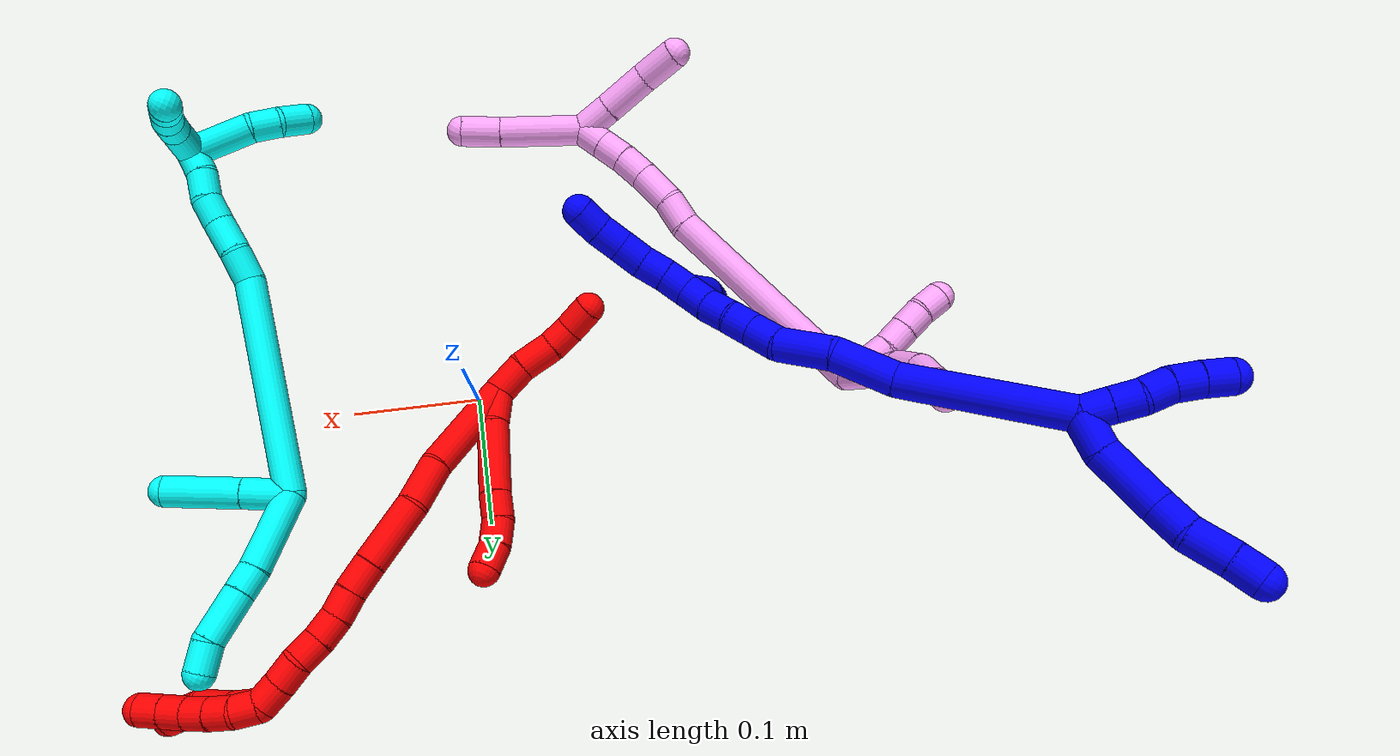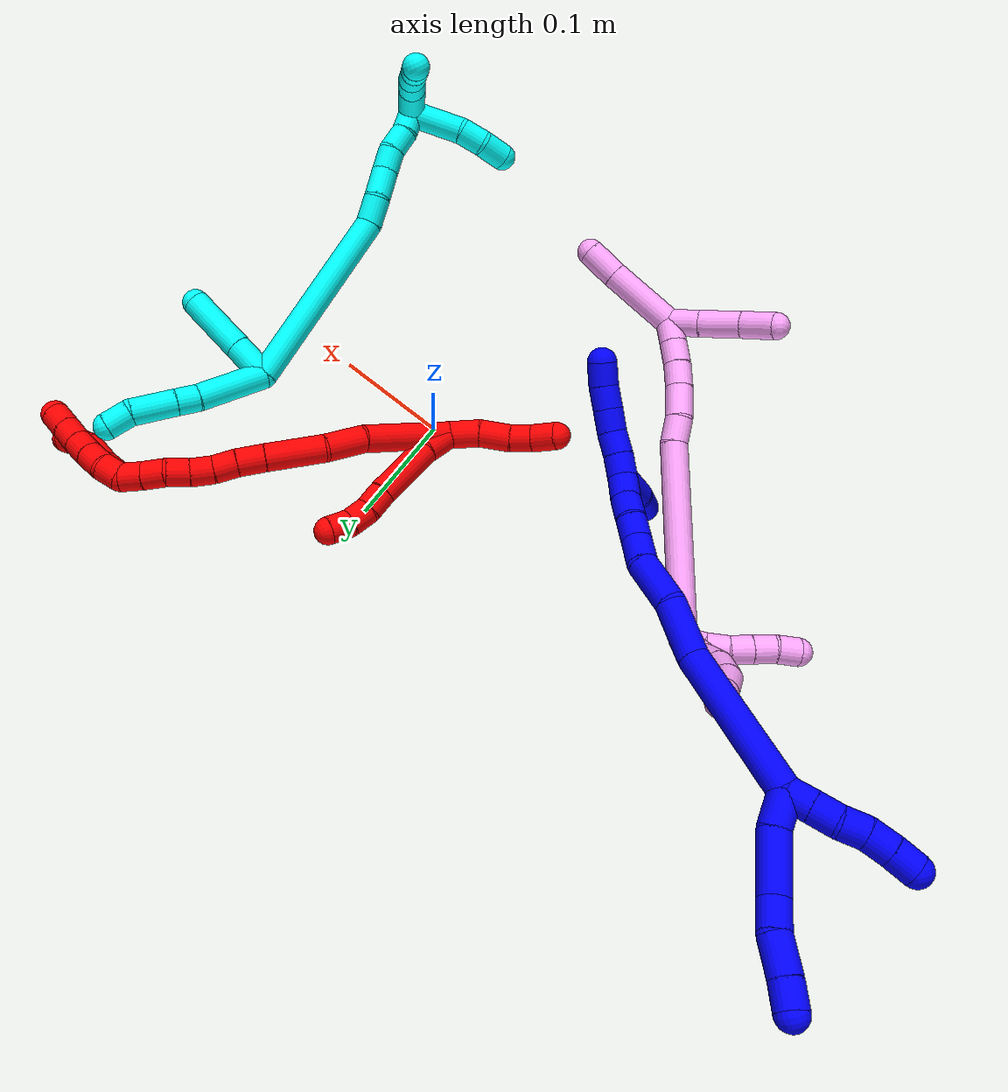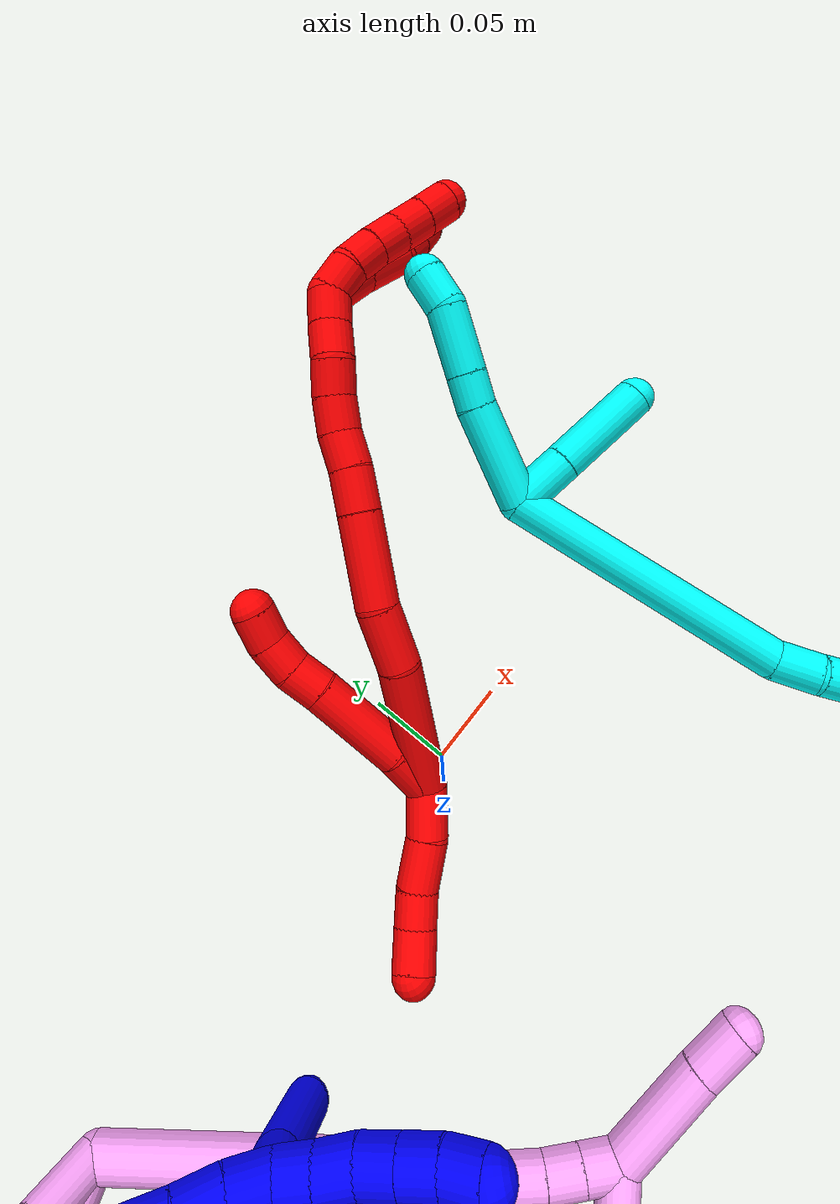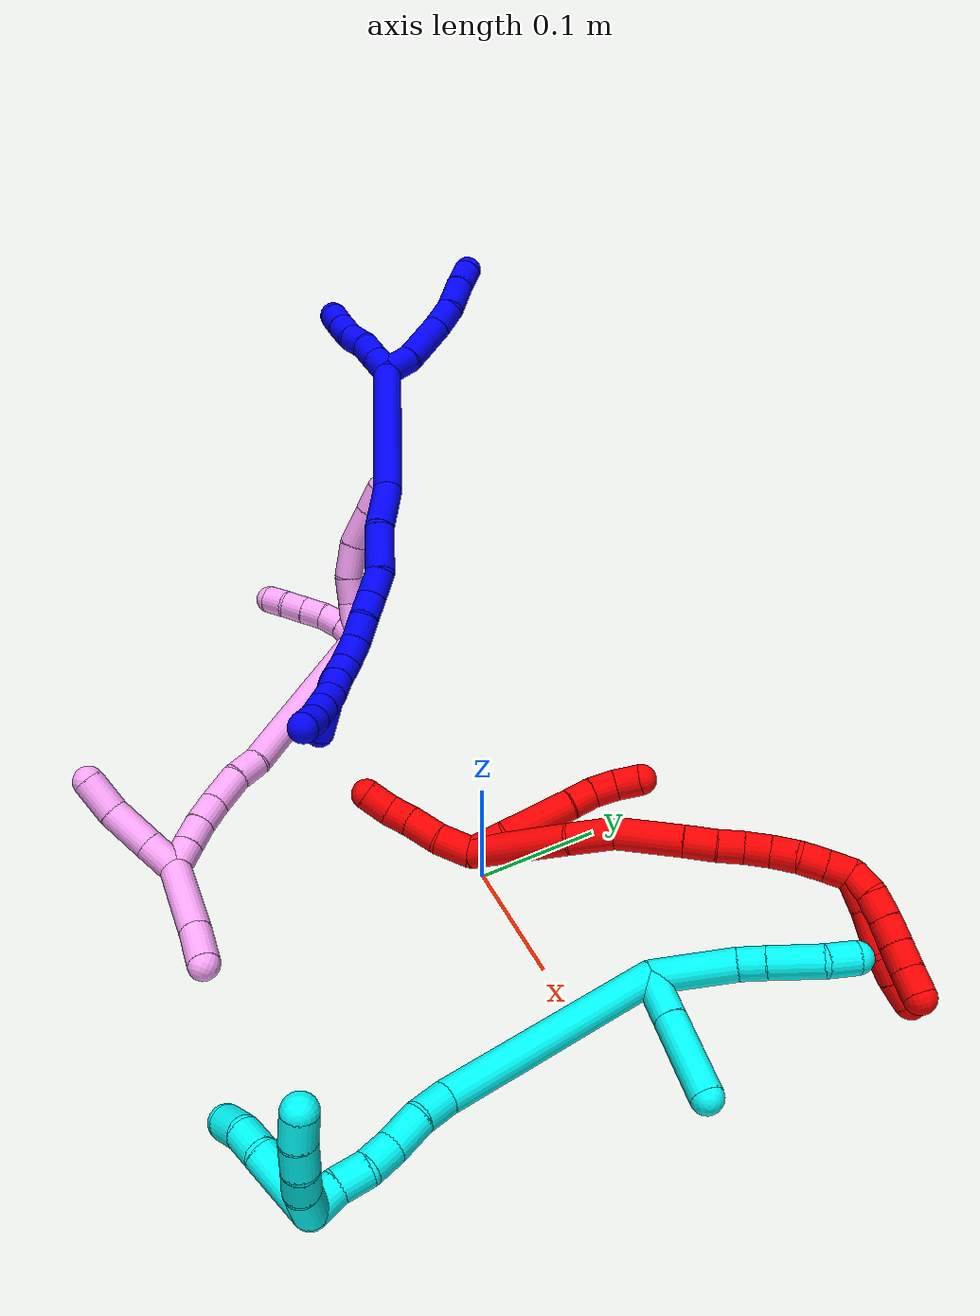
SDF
<sdf version="1.7">
 <world name="default">
  <plugin name="TubeGeneratorPlugin" filename="libtube_generator_plugin.so"/>
  <model name="photoneo_s_sensor">
   <static>1</static>
   <pose>0 0 2 1.57079 1.57079 3.14159</pose>
   <link name="link">
    <inertial><mass>0.1</mass></inertial>
    <sensor name="sensor" type="depth">
     <update_rate>30</update_rate>
     <camera>
      <horizontal_fov>1.22</horizontal_fov>
      <image><width>1920</width><height>1200</height><format>B8G8R8</format></image>
      <clip><near>0.1</near><far>4</far></clip>
      <depth_camera><output>points</output></depth_camera>
     </camera>
     <plugin name="camera_plugin" filename="libgazebo_ros_depth_camera.so">
      <baseline>0.2</baseline>
      <alwaysOn>1</alwaysOn>
      <updateRate>0.0</updateRate>
      <cameraName>camera_ir</cameraName>
      <imageTopicName>/camera/color/image_raw</imageTopicName>
      <cameraInfoTopicName>/camera/color/camera_info</cameraInfoTopicName>
      <depthImageTopicName>/camera/depth/image_raw</depthImageTopicName>
      <depthImageCameraInfoTopicName>/camera/depth/camera_info</depthImageCameraInfoTopicName>
      <pointCloudTopicName>/camera/depth/points</pointCloudTopicName>
      <frameName>fr_optical</frameName>
      <pointCloudCutoff>0.1</pointCloudCutoff>
      <pointCloudCutoffMax>2.0</pointCloudCutoffMax>
      <distortionK1>0</distortionK1>
      <distortionK2>0</distortionK2>
      <distortionK3>0</distortionK3>
      <distortionT1>0</distortionT1>
      <distortionT2>0</distortionT2>
      <CxPrime>0</CxPrime>
      <Cx>0</Cx>
      <Cy>0</Cy>
      <focalLength>0</focalLength>
      <hackBaseline>0</hackBaseline>
     </plugin>
    </sensor>
   </link>
  </model>
  <gravity>0 0 -9.8</gravity>
  <magnetic_field>6e-06 2.3e-05 -4.2e-05</magnetic_field>
  <atmosphere type="adiabatic"/>
  <physics name="default_physics" default="0" type="ode">
   <max_step_size>0.003</max_step_size>
   <real_time_factor>1</real_time_factor>
   <real_time_update_rate>1000</real_time_update_rate>
   <max_contacts>10000</max_contacts>
   <ode>
    <solver>
     <type>quick</type>
     <iters>100</iters>
     <sor>1.3</sor>
     <use_dynamic_moi_rescaling>0</use_dynamic_moi_rescaling>
    </solver>
    <constraints>
     <contact_max_correcting_vel>0</contact_max_correcting_vel>
     <contact_surface_layer>0.001</contact_surface_layer>
     <cfm>0</cfm>
     <erp>0.2</erp>
    </constraints>
   </ode>
  </physics>
  <scene><ambient>0.4 0.4 0.4 1</ambient><background>0.7 0.7 0.7 1</background><shadows>0</shadows></scene>
  <audio><device>default</device></audio>
  <spherical_coordinates>
   <surface_model>EARTH_WGS84</surface_model>
   <latitude_deg>0</latitude_deg>
   <longitude_deg>0</longitude_deg>
   <elevation>0</elevation>
   <heading_deg>0</heading_deg>
  </spherical_coordinates>
  <model name="bin">
   <static>1</static>
   <link name="bottom">
    <collision name="collision-bottom">
     <pose>0 0 -0.01 0 -0 0</pose>
     <geometry><box><size>0.8 0.6 0.02</size></box></geometry>
     <surface>
      <friction><ode><mu>100</mu><mu2>100</mu2></ode></friction>
      <contact><collide_bitmask>65535</collide_bitmask></contact>
     </surface>
    </collision>
   </link>
   <link name="west_wall">
    <collision name="collision-west_wall">
     <pose>-0.41 0 0.1 0 -0 0</pose>
     <geometry><box><size>0.02 0.6 0.2</size></box></geometry>
     <surface>
      <friction><ode><mu>100</mu><mu2>100</mu2></ode></friction>
      <contact><collide_bitmask>65535</collide_bitmask></contact>
     </surface>
    </collision>
   </link>
   <link name="east_wall">
    <collision name="collision-east_wall">
     <pose>0.41 0 0.1 0 -0 0</pose>
     <geometry><box><size>0.02 0.6 0.2</size></box></geometry>
     <surface>
      <friction><ode><mu>100</mu><mu2>100</mu2></ode></friction>
      <contact><collide_bitmask>65535</collide_bitmask></contact>
     </surface>
    </collision>
   </link>
   <link name="south_wall">
    <collision name="collision-south_wall">
     <pose>0 -0.31 0.1 0 -0 0</pose>
     <geometry><box><size>0.8 0.02 0.2</size></box></geometry>
     <surface>
      <friction><ode><mu>100</mu><mu2>100</mu2></ode></friction>
      <contact><collide_bitmask>65535</collide_bitmask></contact>
     </surface>
    </collision>
   </link>
   <link name="north_wall">
    <collision name="collision-north_wall">
     <pose>0 0.31 0.1 0 -0 0</pose>
     <geometry><box><size>0.8 0.02 0.2</size></box></geometry>
     <surface>
      <friction><ode><mu>100</mu><mu2>100</mu2></ode></friction>
      <contact><collide_bitmask>65535</collide_bitmask></contact>
     </surface>
    </collision>
   </link>
  </model>
  <model name="1">
   <static>0</static>
   <link name="1">
    <collision name="collision-cylinder-e_1_2_8">
     <pose>-0.008165 -0.000133 0.010962 0.012176 -0.640165 -0.004036</pose>
     <geometry><cylinder><radius>0.0125</radius><length>0.02734</length></cylinder></geometry>
     <surface>
      <friction><ode><mu>1.16</mu><mu2>1.16</mu2><slip1>0</slip1><slip2>0</slip2></ode></friction>
      <contact><ode><kp>1e+06</kp><kd>1</kd><max_vel>0</max_vel><min_depth>0.001</min_depth></ode></contact>
     </surface>
    </collision>
    <visual name="visual-cylinder-e_1_2_8">
     <pose>-0.008165 -0.000133 0.010962 0.012176 -0.640165 -0.004036</pose>
     <geometry><cylinder><radius>0.0125</radius><length>0.02734</length></cylinder></geometry>
     <material><ambient>0 0 1 1</ambient></material>
    </visual>
    <collision name="collision-cylinder-e_2_8_9">
     <pose>-0.025975 0.004066 0.043347 -0.199563 -0.415559 0.042206</pose>
     <geometry><cylinder><radius>0.0125</radius><length>0.047779</length></cylinder></geometry>
     <surface>
      <friction><ode><mu>1.16</mu><mu2>1.16</mu2><slip1>0</slip1><slip2>0</slip2></ode></friction>
      <contact><ode><kp>1e+06</kp><kd>1</kd><max_vel>0</max_vel><min_depth>0.001</min_depth></ode></contact>
     </surface>
    </collision>
    <visual name="visual-cylinder-e_2_8_9">
     <pose>-0.025975 0.004066 0.043347 -0.199563 -0.415559 0.042206</pose>
     <geometry><cylinder><radius>0.0125</radius><length>0.047779</length></cylinder></geometry>
     <material><ambient>0 0 1 1</ambient></material>
    </visual>
    <collision name="collision-cylinder-e_3_9_10">
     <pose>-0.041065 0.012587 0.074681 -0.399796 -0.468521 0.096624</pose>
     <geometry><cylinder><radius>0.0125</radius><length>0.02412</length></cylinder></geometry>
     <surface>
      <friction><ode><mu>1.16</mu><mu2>1.16</mu2><slip1>0</slip1><slip2>0</slip2></ode></friction>
      <contact><ode><kp>1e+06</kp><kd>1</kd><max_vel>0</max_vel><min_depth>0.001</min_depth></ode></contact>
     </surface>
    </collision>
    <visual name="visual-cylinder-e_3_9_10">
     <pose>-0.041065 0.012587 0.074681 -0.399796 -0.468521 0.096624</pose>
     <geometry><cylinder><radius>0.0125</radius><length>0.02412</length></cylinder></geometry>
     <material><ambient>0 0 1 1</ambient></material>
    </visual>
    <collision name="collision-cylinder-e_4_10_11">
     <pose>-0.049515 0.021856 0.098079 -0.360288 -0.205545 0.037561</pose>
     <geometry><cylinder><radius>0.0125</radius><length>0.029441</length></cylinder></geometry>
     <surface>
      <friction><ode><mu>1.16</mu><mu2>1.16</mu2><slip1>0</slip1><slip2>0</slip2></ode></friction>
      <contact><ode><kp>1e+06</kp><kd>1</kd><max_vel>0</max_vel><min_depth>0.001</min_depth></ode></contact>
     </surface>
    </collision>
    <visual name="visual-cylinder-e_4_10_11">
     <pose>-0.049515 0.021856 0.098079 -0.360288 -0.205545 0.037561</pose>
     <geometry><cylinder><radius>0.0125</radius><length>0.029441</length></cylinder></geometry>
     <material><ambient>0 0 1 1</ambient></material>
    </visual>
    <collision name="collision-cylinder-e_5_11_6">
     <pose>-0.055391 0.030282 0.12127 -0.331969 -0.272665 0.045955</pose>
     <geometry><cylinder><radius>0.0125</radius><length>0.02132</length></cylinder></geometry>
     <surface>
      <friction><ode><mu>1.16</mu><mu2>1.16</mu2><slip1>0</slip1><slip2>0</slip2></ode></friction>
      <contact><ode><kp>1e+06</kp><kd>1</kd><max_vel>0</max_vel><min_depth>0.001</min_depth></ode></contact>
     </surface>
    </collision>
    <visual name="visual-cylinder-e_5_11_6">
     <pose>-0.055391 0.030282 0.12127 -0.331969 -0.272665 0.045955</pose>
     <geometry><cylinder><radius>0.0125</radius><length>0.02132</length></cylinder></geometry>
     <material><ambient>0 0 1 1</ambient></material>
    </visual>
    <collision name="collision-cylinder-e_1_2_12">
     <pose>0.006266 0.003805 0.006801 -0.510161 0.677238 -0.183158</pose>
     <geometry><cylinder><radius>0.0125</radius><length>0.02</length></cylinder></geometry>
     <surface>
      <friction><ode><mu>1.16</mu><mu2>1.16</mu2><slip1>0</slip1><slip2>0</slip2></ode></friction>
      <contact><ode><kp>1e+06</kp><kd>1</kd><max_vel>0</max_vel><min_depth>0.001</min_depth></ode></contact>
     </surface>
    </collision>
    <visual name="visual-cylinder-e_1_2_12">
     <pose>0.006266 0.003805 0.006801 -0.510161 0.677238 -0.183158</pose>
     <geometry><cylinder><radius>0.0125</radius><length>0.02</length></cylinder></geometry>
     <material><ambient>0 0 1 1</ambient></material>
    </visual>
    <collision name="collision-cylinder-e_2_12_13">
     <pose>0.01857 0.011594 0.020508 -0.523094 0.648123 -0.179346</pose>
     <geometry><cylinder><radius>0.0125</radius><length>0.02</length></cylinder></geometry>
     <surface>
      <friction><ode><mu>1.16</mu><mu2>1.16</mu2><slip1>0</slip1><slip2>0</slip2></ode></friction>
      <contact><ode><kp>1e+06</kp><kd>1</kd><max_vel>0</max_vel><min_depth>0.001</min_depth></ode></contact>
     </surface>
    </collision>
    <visual name="visual-cylinder-e_2_12_13">
     <pose>0.01857 0.011594 0.020508 -0.523094 0.648123 -0.179346</pose>
     <geometry><cylinder><radius>0.0125</radius><length>0.02</length></cylinder></geometry>
     <material><ambient>0 0 1 1</ambient></material>
    </visual>
    <collision name="collision-cylinder-e_3_13_14">
     <pose>0.032335 0.017809 0.033354 -0.359532 0.883269 -0.171413</pose>
     <geometry><cylinder><radius>0.0125</radius><length>0.02</length></cylinder></geometry>
     <surface>
      <friction><ode><mu>1.16</mu><mu2>1.16</mu2><slip1>0</slip1><slip2>0</slip2></ode></friction>
      <contact><ode><kp>1e+06</kp><kd>1</kd><max_vel>0</max_vel><min_depth>0.001</min_depth></ode></contact>
     </surface>
    </collision>
    <visual name="visual-cylinder-e_3_13_14">
     <pose>0.032335 0.017809 0.033354 -0.359532 0.883269 -0.171413</pose>
     <geometry><cylinder><radius>0.0125</radius><length>0.02</length></cylinder></geometry>
     <material><ambient>0 0 1 1</ambient></material>
    </visual>
    <collision name="collision-cylinder-e_4_14_15">
     <pose>0.045948 0.022579 0.046972 -0.319208 0.629155 -0.10466</pose>
     <geometry><cylinder><radius>0.0125</radius><length>0.02</length></cylinder></geometry>
     <surface>
      <friction><ode><mu>1.16</mu><mu2>1.16</mu2><slip1>0</slip1><slip2>0</slip2></ode></friction>
      <contact><ode><kp>1e+06</kp><kd>1</kd><max_vel>0</max_vel><min_depth>0.001</min_depth></ode></contact>
     </surface>
    </collision>
    <visual name="visual-cylinder-e_4_14_15">
     <pose>0.045948 0.022579 0.046972 -0.319208 0.629155 -0.10466</pose>
     <geometry><cylinder><radius>0.0125</radius><length>0.02</length></cylinder></geometry>
     <material><ambient>0 0 1 1</ambient></material>
    </visual>
    <collision name="collision-cylinder-e_5_15_5">
     <pose>0.057237 0.027337 0.062763 -0.267123 0.57102 -0.078837</pose>
     <geometry><cylinder><radius>0.0125</radius><length>0.02</length></cylinder></geometry>
     <surface>
      <friction><ode><mu>1.16</mu><mu2>1.16</mu2><slip1>0</slip1><slip2>0</slip2></ode></friction>
      <contact><ode><kp>1e+06</kp><kd>1</kd><max_vel>0</max_vel><min_depth>0.001</min_depth></ode></contact>
     </surface>
    </collision>
    <visual name="visual-cylinder-e_5_15_5">
     <pose>0.057237 0.027337 0.062763 -0.267123 0.57102 -0.078837</pose>
     <geometry><cylinder><radius>0.0125</radius><length>0.02</length></cylinder></geometry>
     <material><ambient>0 0 1 1</ambient></material>
    </visual>
    <collision name="collision-cylinder-e_1_2_16">
     <pose>-0.005027 -0.031028 -0.053499 2.61602 -0.081112 -0.299435</pose>
     <geometry><cylinder><radius>0.0125</radius><length>0.124099</length></cylinder></geometry>
     <surface>
      <friction><ode><mu>1.16</mu><mu2>1.16</mu2><slip1>0</slip1><slip2>0</slip2></ode></friction>
      <contact><ode><kp>1e+06</kp><kd>1</kd><max_vel>0</max_vel><min_depth>0.001</min_depth></ode></contact>
     </surface>
    </collision>
    <visual name="visual-cylinder-e_1_2_16">
     <pose>-0.005027 -0.031028 -0.053499 2.61602 -0.081112 -0.299435</pose>
     <geometry><cylinder><radius>0.0125</radius><length>0.124099</length></cylinder></geometry>
     <material><ambient>0 0 1 1</ambient></material>
    </visual>
    <collision name="collision-cylinder-e_2_16_17">
     <pose>-0.010328 -0.067525 -0.12942 2.90236 -0.01184 -0.098436</pose>
     <geometry><cylinder><radius>0.0125</radius><length>0.046162</length></cylinder></geometry>
     <surface>
      <friction><ode><mu>1.16</mu><mu2>1.16</mu2><slip1>0</slip1><slip2>0</slip2></ode></friction>
      <contact><ode><kp>1e+06</kp><kd>1</kd><max_vel>0</max_vel><min_depth>0.001</min_depth></ode></contact>
     </surface>
    </collision>
    <visual name="visual-cylinder-e_2_16_17">
     <pose>-0.010328 -0.067525 -0.12942 2.90236 -0.01184 -0.098436</pose>
     <geometry><cylinder><radius>0.0125</radius><length>0.046162</length></cylinder></geometry>
     <material><ambient>0 0 1 1</ambient></material>
    </visual>
    <collision name="collision-cylinder-e_3_17_18">
     <pose>-0.012603 -0.08352 -0.169937 2.61474 -0.095317 -0.350071</pose>
     <geometry><cylinder><radius>0.0125</radius><length>0.042058</length></cylinder></geometry>
     <surface>
      <friction><ode><mu>1.16</mu><mu2>1.16</mu2><slip1>0</slip1><slip2>0</slip2></ode></friction>
      <contact><ode><kp>1e+06</kp><kd>1</kd><max_vel>0</max_vel><min_depth>0.001</min_depth></ode></contact>
     </surface>
    </collision>
    <visual name="visual-cylinder-e_3_17_18">
     <pose>-0.012603 -0.08352 -0.169937 2.61474 -0.095317 -0.350071</pose>
     <geometry><cylinder><radius>0.0125</radius><length>0.042058</length></cylinder></geometry>
     <material><ambient>0 0 1 1</ambient></material>
    </visual>
    <collision name="collision-cylinder-e_4_18_19">
     <pose>-0.011765 -0.099534 -0.198106 2.64281 0.242655 0.892946</pose>
     <geometry><cylinder><radius>0.0125</radius><length>0.023637</length></cylinder></geometry>
     <surface>
      <friction><ode><mu>1.16</mu><mu2>1.16</mu2><slip1>0</slip1><slip2>0</slip2></ode></friction>
      <contact><ode><kp>1e+06</kp><kd>1</kd><max_vel>0</max_vel><min_depth>0.001</min_depth></ode></contact>
     </surface>
    </collision>
    <visual name="visual-cylinder-e_4_18_19">
     <pose>-0.011765 -0.099534 -0.198106 2.64281 0.242655 0.892946</pose>
     <geometry><cylinder><radius>0.0125</radius><length>0.023637</length></cylinder></geometry>
     <material><ambient>0 0 1 1</ambient></material>
    </visual>
    <collision name="collision-cylinder-e_5_19_20">
     <pose>-0.007116 -0.108549 -0.217754 2.78858 0.175472 0.916328</pose>
     <geometry><cylinder><radius>0.0125</radius><length>0.020722</length></cylinder></geometry>
     <surface>
      <friction><ode><mu>1.16</mu><mu2>1.16</mu2><slip1>0</slip1><slip2>0</slip2></ode></friction>
      <contact><ode><kp>1e+06</kp><kd>1</kd><max_vel>0</max_vel><min_depth>0.001</min_depth></ode></contact>
     </surface>
    </collision>
    <visual name="visual-cylinder-e_5_19_20">
     <pose>-0.007116 -0.108549 -0.217754 2.78858 0.175472 0.916328</pose>
     <geometry><cylinder><radius>0.0125</radius><length>0.020722</length></cylinder></geometry>
     <material><ambient>0 0 1 1</ambient></material>
    </visual>
    <collision name="collision-cylinder-e_6_20_21">
     <pose>-0.002862 -0.117209 -0.236367 2.62516 0.231019 0.827847</pose>
     <geometry><cylinder><radius>0.0125</radius><length>0.021359</length></cylinder></geometry>
     <surface>
      <friction><ode><mu>1.16</mu><mu2>1.16</mu2><slip1>0</slip1><slip2>0</slip2></ode></friction>
      <contact><ode><kp>1e+06</kp><kd>1</kd><max_vel>0</max_vel><min_depth>0.001</min_depth></ode></contact>
     </surface>
    </collision>
    <visual name="visual-cylinder-e_6_20_21">
     <pose>-0.002862 -0.117209 -0.236367 2.62516 0.231019 0.827847</pose>
     <geometry><cylinder><radius>0.0125</radius><length>0.021359</length></cylinder></geometry>
     <material><ambient>0 0 1 1</ambient></material>
    </visual>
    <collision name="collision-cylinder-e_7_21_1">
     <pose>0.002671 -0.126232 -0.255201 2.76355 0.285 1.28696</pose>
     <geometry><cylinder><radius>0.0125</radius><length>0.021962</length></cylinder></geometry>
     <surface>
      <friction><ode><mu>1.16</mu><mu2>1.16</mu2><slip1>0</slip1><slip2>0</slip2></ode></friction>
      <contact><ode><kp>1e+06</kp><kd>1</kd><max_vel>0</max_vel><min_depth>0.001</min_depth></ode></contact>
     </surface>
    </collision>
    <visual name="visual-cylinder-e_7_21_1">
     <pose>0.002671 -0.126232 -0.255201 2.76355 0.285 1.28696</pose>
     <geometry><cylinder><radius>0.0125</radius><length>0.021962</length></cylinder></geometry>
     <material><ambient>0 0 1 1</ambient></material>
    </visual>
    <collision name="collision-cylinder-e_1_1_22">
     <pose>0.016511 -0.143966 -0.259169 1.17249 0.621311 0.420148</pose>
     <geometry><cylinder><radius>0.0125</radius><length>0.036945</length></cylinder></geometry>
     <surface>
      <friction><ode><mu>1.16</mu><mu2>1.16</mu2><slip1>0</slip1><slip2>0</slip2></ode></friction>
      <contact><ode><kp>1e+06</kp><kd>1</kd><max_vel>0</max_vel><min_depth>0.001</min_depth></ode></contact>
     </surface>
    </collision>
    <visual name="visual-cylinder-e_1_1_22">
     <pose>0.016511 -0.143966 -0.259169 1.17249 0.621311 0.420148</pose>
     <geometry><cylinder><radius>0.0125</radius><length>0.036945</length></cylinder></geometry>
     <material><ambient>0 0 1 1</ambient></material>
    </visual>
    <collision name="collision-cylinder-e_2_22_4">
     <pose>0.041719 -0.185784 -0.251747 1.51379 0.476286 0.45079</pose>
     <geometry><cylinder><radius>0.0125</radius><length>0.063055</length></cylinder></geometry>
     <surface>
      <friction><ode><mu>1.16</mu><mu2>1.16</mu2><slip1>0</slip1><slip2>0</slip2></ode></friction>
      <contact><ode><kp>1e+06</kp><kd>1</kd><max_vel>0</max_vel><min_depth>0.001</min_depth></ode></contact>
     </surface>
    </collision>
    <visual name="visual-cylinder-e_2_22_4">
     <pose>0.041719 -0.185784 -0.251747 1.51379 0.476286 0.45079</pose>
     <geometry><cylinder><radius>0.0125</radius><length>0.063055</length></cylinder></geometry>
     <material><ambient>0 0 1 1</ambient></material>
    </visual>
    <collision name="collision-cylinder-e_1_1_23">
     <pose>0.006789 -0.130184 -0.274941 3.13538 0.1033 3.02151</pose>
     <geometry><cylinder><radius>0.0125</radius><length>0.02</length></cylinder></geometry>
     <surface>
      <friction><ode><mu>1.16</mu><mu2>1.16</mu2><slip1>0</slip1><slip2>0</slip2></ode></friction>
      <contact><ode><kp>1e+06</kp><kd>1</kd><max_vel>0</max_vel><min_depth>0.001</min_depth></ode></contact>
     </surface>
    </collision>
    <visual name="visual-cylinder-e_1_1_23">
     <pose>0.006789 -0.130184 -0.274941 3.13538 0.1033 3.02151</pose>
     <geometry><cylinder><radius>0.0125</radius><length>0.02</length></cylinder></geometry>
     <material><ambient>0 0 1 1</ambient></material>
    </visual>
    <collision name="collision-cylinder-e_2_23_24">
     <pose>0.007911 -0.130311 -0.294887 3.13506 0.009084 1.89507</pose>
     <geometry><cylinder><radius>0.0125</radius><length>0.02</length></cylinder></geometry>
     <surface>
      <friction><ode><mu>1.16</mu><mu2>1.16</mu2><slip1>0</slip1><slip2>0</slip2></ode></friction>
      <contact><ode><kp>1e+06</kp><kd>1</kd><max_vel>0</max_vel><min_depth>0.001</min_depth></ode></contact>
     </surface>
    </collision>
    <visual name="visual-cylinder-e_2_23_24">
     <pose>0.007911 -0.130311 -0.294887 3.13506 0.009084 1.89507</pose>
     <geometry><cylinder><radius>0.0125</radius><length>0.02</length></cylinder></geometry>
     <material><ambient>0 0 1 1</ambient></material>
    </visual>
    <collision name="collision-cylinder-e_3_24_25">
     <pose>0.008295 -0.128399 -0.314685 -2.94246 0.029329 -0.291539</pose>
     <geometry><cylinder><radius>0.0125</radius><length>0.02</length></cylinder></geometry>
     <surface>
      <friction><ode><mu>1.16</mu><mu2>1.16</mu2><slip1>0</slip1><slip2>0</slip2></ode></friction>
      <contact><ode><kp>1e+06</kp><kd>1</kd><max_vel>0</max_vel><min_depth>0.001</min_depth></ode></contact>
     </surface>
    </collision>
    <visual name="visual-cylinder-e_3_24_25">
     <pose>0.008295 -0.128399 -0.314685 -2.94246 0.029329 -0.291539</pose>
     <geometry><cylinder><radius>0.0125</radius><length>0.02</length></cylinder></geometry>
     <material><ambient>0 0 1 1</ambient></material>
    </visual>
    <collision name="collision-cylinder-e_4_25_26">
     <pose>0.008721 -0.124391 -0.334274 -2.93714 0.013279 -0.129272</pose>
     <geometry><cylinder><radius>0.0125</radius><length>0.02</length></cylinder></geometry>
     <surface>
      <friction><ode><mu>1.16</mu><mu2>1.16</mu2><slip1>0</slip1><slip2>0</slip2></ode></friction>
      <contact><ode><kp>1e+06</kp><kd>1</kd><max_vel>0</max_vel><min_depth>0.001</min_depth></ode></contact>
     </surface>
    </collision>
    <visual name="visual-cylinder-e_4_25_26">
     <pose>0.008721 -0.124391 -0.334274 -2.93714 0.013279 -0.129272</pose>
     <geometry><cylinder><radius>0.0125</radius><length>0.02</length></cylinder></geometry>
     <material><ambient>0 0 1 1</ambient></material>
    </visual>
    <collision name="collision-cylinder-e_5_26_3">
     <pose>0.009501 -0.118753 -0.353368 -2.77159 0.064677 -0.342344</pose>
     <geometry><cylinder><radius>0.0125</radius><length>0.02</length></cylinder></geometry>
     <surface>
      <friction><ode><mu>1.16</mu><mu2>1.16</mu2><slip1>0</slip1><slip2>0</slip2></ode></friction>
      <contact><ode><kp>1e+06</kp><kd>1</kd><max_vel>0</max_vel><min_depth>0.001</min_depth></ode></contact>
     </surface>
    </collision>
    <visual name="visual-cylinder-e_5_26_3">
     <pose>0.009501 -0.118753 -0.353368 -2.77159 0.064677 -0.342344</pose>
     <geometry><cylinder><radius>0.0125</radius><length>0.02</length></cylinder></geometry>
     <material><ambient>0 0 1 1</ambient></material>
    </visual>
    <collision name="collision-sphere-3">
     <pose>0.010147 -0.115144 -0.362672 0 -0 0</pose>
     <geometry><sphere><radius>0.0125</radius></sphere></geometry>
     <surface>
      <friction><ode><mu>1.16</mu><mu2>1.16</mu2><slip1>0</slip1><slip2>0</slip2></ode></friction>
      <contact><ode><kp>1e+06</kp><kd>1</kd><max_vel>0</max_vel><min_depth>0.001</min_depth></ode></contact>
     </surface>
    </collision>
    <visual name="visual-sphere-3">
     <pose>0.010147 -0.115144 -0.362672 0 -0 0</pose>
     <geometry><sphere><radius>0.0125</radius></sphere></geometry>
     <material><ambient>0 0 1 1</ambient></material>
    </visual>
    <collision name="collision-sphere-26">
     <pose>0.008854 -0.122361 -0.344064 0 -0 0</pose>
     <geometry><sphere><radius>0.0125</radius></sphere></geometry>
     <surface>
      <friction><ode><mu>1.16</mu><mu2>1.16</mu2><slip1>0</slip1><slip2>0</slip2></ode></friction>
      <contact><ode><kp>1e+06</kp><kd>1</kd><max_vel>0</max_vel><min_depth>0.001</min_depth></ode></contact>
     </surface>
    </collision>
    <visual name="visual-sphere-26">
     <pose>0.008854 -0.122361 -0.344064 0 -0 0</pose>
     <geometry><sphere><radius>0.0125</radius></sphere></geometry>
     <material><ambient>0 0 1 1</ambient></material>
    </visual>
    <collision name="collision-sphere-25">
     <pose>0.008589 -0.126421 -0.324483 0 -0 0</pose>
     <geometry><sphere><radius>0.0125</radius></sphere></geometry>
     <surface>
      <friction><ode><mu>1.16</mu><mu2>1.16</mu2><slip1>0</slip1><slip2>0</slip2></ode></friction>
      <contact><ode><kp>1e+06</kp><kd>1</kd><max_vel>0</max_vel><min_depth>0.001</min_depth></ode></contact>
     </surface>
    </collision>
    <visual name="visual-sphere-25">
     <pose>0.008589 -0.126421 -0.324483 0 -0 0</pose>
     <geometry><sphere><radius>0.0125</radius></sphere></geometry>
     <material><ambient>0 0 1 1</ambient></material>
    </visual>
    <collision name="collision-sphere-24">
     <pose>0.008002 -0.130376 -0.304886 0 -0 0</pose>
     <geometry><sphere><radius>0.0125</radius></sphere></geometry>
     <surface>
      <friction><ode><mu>1.16</mu><mu2>1.16</mu2><slip1>0</slip1><slip2>0</slip2></ode></friction>
      <contact><ode><kp>1e+06</kp><kd>1</kd><max_vel>0</max_vel><min_depth>0.001</min_depth></ode></contact>
     </surface>
    </collision>
    <visual name="visual-sphere-24">
     <pose>0.008002 -0.130376 -0.304886 0 -0 0</pose>
     <geometry><sphere><radius>0.0125</radius></sphere></geometry>
     <material><ambient>0 0 1 1</ambient></material>
    </visual>
    <collision name="collision-sphere-23">
     <pose>0.00782 -0.130245 -0.284888 0 -0 0</pose>
     <geometry><sphere><radius>0.0125</radius></sphere></geometry>
     <surface>
      <friction><ode><mu>1.16</mu><mu2>1.16</mu2><slip1>0</slip1><slip2>0</slip2></ode></friction>
      <contact><ode><kp>1e+06</kp><kd>1</kd><max_vel>0</max_vel><min_depth>0.001</min_depth></ode></contact>
     </surface>
    </collision>
    <visual name="visual-sphere-23">
     <pose>0.00782 -0.130245 -0.284888 0 -0 0</pose>
     <geometry><sphere><radius>0.0125</radius></sphere></geometry>
     <material><ambient>0 0 1 1</ambient></material>
    </visual>
    <collision name="collision-sphere-4">
     <pose>0.056173 -0.213757 -0.25015 0 -0 0</pose>
     <geometry><sphere><radius>0.0125</radius></sphere></geometry>
     <surface>
      <friction><ode><mu>1.16</mu><mu2>1.16</mu2><slip1>0</slip1><slip2>0</slip2></ode></friction>
      <contact><ode><kp>1e+06</kp><kd>1</kd><max_vel>0</max_vel><min_depth>0.001</min_depth></ode></contact>
     </surface>
    </collision>
    <visual name="visual-sphere-4">
     <pose>0.056173 -0.213757 -0.25015 0 -0 0</pose>
     <geometry><sphere><radius>0.0125</radius></sphere></geometry>
     <material><ambient>0 0 1 1</ambient></material>
    </visual>
    <collision name="collision-sphere-22">
     <pose>0.027264 -0.157811 -0.253343 0 -0 0</pose>
     <geometry><sphere><radius>0.0125</radius></sphere></geometry>
     <surface>
      <friction><ode><mu>1.16</mu><mu2>1.16</mu2><slip1>0</slip1><slip2>0</slip2></ode></friction>
      <contact><ode><kp>1e+06</kp><kd>1</kd><max_vel>0</max_vel><min_depth>0.001</min_depth></ode></contact>
     </surface>
    </collision>
    <visual name="visual-sphere-22">
     <pose>0.027264 -0.157811 -0.253343 0 -0 0</pose>
     <geometry><sphere><radius>0.0125</radius></sphere></geometry>
     <material><ambient>0 0 1 1</ambient></material>
    </visual>
    <collision name="collision-sphere-1">
     <pose>0.005758 -0.130122 -0.264995 0 -0 0</pose>
     <geometry><sphere><radius>0.0125</radius></sphere></geometry>
     <surface>
      <friction><ode><mu>1.16</mu><mu2>1.16</mu2><slip1>0</slip1><slip2>0</slip2></ode></friction>
      <contact><ode><kp>1e+06</kp><kd>1</kd><max_vel>0</max_vel><min_depth>0.001</min_depth></ode></contact>
     </surface>
    </collision>
    <visual name="visual-sphere-1">
     <pose>0.005758 -0.130122 -0.264995 0 -0 0</pose>
     <geometry><sphere><radius>0.0125</radius></sphere></geometry>
     <material><ambient>0 0 1 1</ambient></material>
    </visual>
    <collision name="collision-sphere-21">
     <pose>-0.000417 -0.122343 -0.245407 0 -0 0</pose>
     <geometry><sphere><radius>0.0125</radius></sphere></geometry>
     <surface>
      <friction><ode><mu>1.16</mu><mu2>1.16</mu2><slip1>0</slip1><slip2>0</slip2></ode></friction>
      <contact><ode><kp>1e+06</kp><kd>1</kd><max_vel>0</max_vel><min_depth>0.001</min_depth></ode></contact>
     </surface>
    </collision>
    <visual name="visual-sphere-21">
     <pose>-0.000417 -0.122343 -0.245407 0 -0 0</pose>
     <geometry><sphere><radius>0.0125</radius></sphere></geometry>
     <material><ambient>0 0 1 1</ambient></material>
    </visual>
    <collision name="collision-sphere-6">
     <pose>-0.058261 0.033628 0.130976 0 -0 0</pose>
     <geometry><sphere><radius>0.0125</radius></sphere></geometry>
     <surface>
      <friction><ode><mu>1.16</mu><mu2>1.16</mu2><slip1>0</slip1><slip2>0</slip2></ode></friction>
      <contact><ode><kp>1e+06</kp><kd>1</kd><max_vel>0</max_vel><min_depth>0.001</min_depth></ode></contact>
     </surface>
    </collision>
    <visual name="visual-sphere-6">
     <pose>-0.058261 0.033628 0.130976 0 -0 0</pose>
     <geometry><sphere><radius>0.0125</radius></sphere></geometry>
     <material><ambient>0 0 1 1</ambient></material>
    </visual>
    <collision name="collision-sphere-11">
     <pose>-0.05252 0.026936 0.111564 0 -0 0</pose>
     <geometry><sphere><radius>0.0125</radius></sphere></geometry>
     <surface>
      <friction><ode><mu>1.16</mu><mu2>1.16</mu2><slip1>0</slip1><slip2>0</slip2></ode></friction>
      <contact><ode><kp>1e+06</kp><kd>1</kd><max_vel>0</max_vel><min_depth>0.001</min_depth></ode></contact>
     </surface>
    </collision>
    <visual name="visual-sphere-11">
     <pose>-0.05252 0.026936 0.111564 0 -0 0</pose>
     <geometry><sphere><radius>0.0125</radius></sphere></geometry>
     <material><ambient>0 0 1 1</ambient></material>
    </visual>
    <collision name="collision-sphere-10">
     <pose>-0.046511 0.016775 0.084593 0 -0 0</pose>
     <geometry><sphere><radius>0.0125</radius></sphere></geometry>
     <surface>
      <friction><ode><mu>1.16</mu><mu2>1.16</mu2><slip1>0</slip1><slip2>0</slip2></ode></friction>
      <contact><ode><kp>1e+06</kp><kd>1</kd><max_vel>0</max_vel><min_depth>0.001</min_depth></ode></contact>
     </surface>
    </collision>
    <visual name="visual-sphere-10">
     <pose>-0.046511 0.016775 0.084593 0 -0 0</pose>
     <geometry><sphere><radius>0.0125</radius></sphere></geometry>
     <material><ambient>0 0 1 1</ambient></material>
    </visual>
    <collision name="collision-sphere-9">
     <pose>-0.035619 0.008399 0.06477 0 -0 0</pose>
     <geometry><sphere><radius>0.0125</radius></sphere></geometry>
     <surface>
      <friction><ode><mu>1.16</mu><mu2>1.16</mu2><slip1>0</slip1><slip2>0</slip2></ode></friction>
      <contact><ode><kp>1e+06</kp><kd>1</kd><max_vel>0</max_vel><min_depth>0.001</min_depth></ode></contact>
     </surface>
    </collision>
    <visual name="visual-sphere-9">
     <pose>-0.035619 0.008399 0.06477 0 -0 0</pose>
     <geometry><sphere><radius>0.0125</radius></sphere></geometry>
     <material><ambient>0 0 1 1</ambient></material>
    </visual>
    <collision name="collision-sphere-2">
     <geometry><sphere><radius>0.0125</radius></sphere></geometry>
     <surface>
      <friction><ode><mu>1.16</mu><mu2>1.16</mu2><slip1>0</slip1><slip2>0</slip2></ode></friction>
      <contact><ode><kp>1e+06</kp><kd>1</kd><max_vel>0</max_vel><min_depth>0.001</min_depth></ode></contact>
     </surface>
    </collision>
    <visual name="visual-sphere-2">
     <geometry><sphere><radius>0.0125</radius></sphere></geometry>
     <material><ambient>0 0 1 1</ambient></material>
    </visual>
    <collision name="collision-sphere-19">
     <pose>-0.008925 -0.105022 -0.208181 0 -0 0</pose>
     <geometry><sphere><radius>0.0125</radius></sphere></geometry>
     <surface>
      <friction><ode><mu>1.16</mu><mu2>1.16</mu2><slip1>0</slip1><slip2>0</slip2></ode></friction>
      <contact><ode><kp>1e+06</kp><kd>1</kd><max_vel>0</max_vel><min_depth>0.001</min_depth></ode></contact>
     </surface>
    </collision>
    <visual name="visual-sphere-19">
     <pose>-0.008925 -0.105022 -0.208181 0 -0 0</pose>
     <geometry><sphere><radius>0.0125</radius></sphere></geometry>
     <material><ambient>0 0 1 1</ambient></material>
    </visual>
    <collision name="collision-sphere-8">
     <pose>-0.016331 -0.000267 0.021925 0 -0 0</pose>
     <geometry><sphere><radius>0.0125</radius></sphere></geometry>
     <surface>
      <friction><ode><mu>1.16</mu><mu2>1.16</mu2><slip1>0</slip1><slip2>0</slip2></ode></friction>
      <contact><ode><kp>1e+06</kp><kd>1</kd><max_vel>0</max_vel><min_depth>0.001</min_depth></ode></contact>
     </surface>
    </collision>
    <visual name="visual-sphere-8">
     <pose>-0.016331 -0.000267 0.021925 0 -0 0</pose>
     <geometry><sphere><radius>0.0125</radius></sphere></geometry>
     <material><ambient>0 0 1 1</ambient></material>
    </visual>
    <collision name="collision-sphere-12">
     <pose>0.012533 0.007611 0.013601 0 -0 0</pose>
     <geometry><sphere><radius>0.0125</radius></sphere></geometry>
     <surface>
      <friction><ode><mu>1.16</mu><mu2>1.16</mu2><slip1>0</slip1><slip2>0</slip2></ode></friction>
      <contact><ode><kp>1e+06</kp><kd>1</kd><max_vel>0</max_vel><min_depth>0.001</min_depth></ode></contact>
     </surface>
    </collision>
    <visual name="visual-sphere-12">
     <pose>0.012533 0.007611 0.013601 0 -0 0</pose>
     <geometry><sphere><radius>0.0125</radius></sphere></geometry>
     <material><ambient>0 0 1 1</ambient></material>
    </visual>
    <collision name="collision-sphere-13">
     <pose>0.024607 0.015576 0.027414 0 -0 0</pose>
     <geometry><sphere><radius>0.0125</radius></sphere></geometry>
     <surface>
      <friction><ode><mu>1.16</mu><mu2>1.16</mu2><slip1>0</slip1><slip2>0</slip2></ode></friction>
      <contact><ode><kp>1e+06</kp><kd>1</kd><max_vel>0</max_vel><min_depth>0.001</min_depth></ode></contact>
     </surface>
    </collision>
    <visual name="visual-sphere-13">
     <pose>0.024607 0.015576 0.027414 0 -0 0</pose>
     <geometry><sphere><radius>0.0125</radius></sphere></geometry>
     <material><ambient>0 0 1 1</ambient></material>
    </visual>
    <collision name="collision-sphere-14">
     <pose>0.040063 0.020042 0.039295 0 -0 0</pose>
     <geometry><sphere><radius>0.0125</radius></sphere></geometry>
     <surface>
      <friction><ode><mu>1.16</mu><mu2>1.16</mu2><slip1>0</slip1><slip2>0</slip2></ode></friction>
      <contact><ode><kp>1e+06</kp><kd>1</kd><max_vel>0</max_vel><min_depth>0.001</min_depth></ode></contact>
     </surface>
    </collision>
    <visual name="visual-sphere-14">
     <pose>0.040063 0.020042 0.039295 0 -0 0</pose>
     <geometry><sphere><radius>0.0125</radius></sphere></geometry>
     <material><ambient>0 0 1 1</ambient></material>
    </visual>
    <collision name="collision-sphere-15">
     <pose>0.051832 0.025116 0.054648 0 -0 0</pose>
     <geometry><sphere><radius>0.0125</radius></sphere></geometry>
     <surface>
      <friction><ode><mu>1.16</mu><mu2>1.16</mu2><slip1>0</slip1><slip2>0</slip2></ode></friction>
      <contact><ode><kp>1e+06</kp><kd>1</kd><max_vel>0</max_vel><min_depth>0.001</min_depth></ode></contact>
     </surface>
    </collision>
    <visual name="visual-sphere-15">
     <pose>0.051832 0.025116 0.054648 0 -0 0</pose>
     <geometry><sphere><radius>0.0125</radius></sphere></geometry>
     <material><ambient>0 0 1 1</ambient></material>
    </visual>
    <collision name="collision-sphere-5">
     <pose>0.062642 0.029558 0.070879 0 -0 0</pose>
     <geometry><sphere><radius>0.0125</radius></sphere></geometry>
     <surface>
      <friction><ode><mu>1.16</mu><mu2>1.16</mu2><slip1>0</slip1><slip2>0</slip2></ode></friction>
      <contact><ode><kp>1e+06</kp><kd>1</kd><max_vel>0</max_vel><min_depth>0.001</min_depth></ode></contact>
     </surface>
    </collision>
    <visual name="visual-sphere-5">
     <pose>0.062642 0.029558 0.070879 0 -0 0</pose>
     <geometry><sphere><radius>0.0125</radius></sphere></geometry>
     <material><ambient>0 0 1 1</ambient></material>
    </visual>
    <collision name="collision-sphere-16">
     <pose>-0.010055 -0.062057 -0.106998 0 -0 0</pose>
     <geometry><sphere><radius>0.0125</radius></sphere></geometry>
     <surface>
      <friction><ode><mu>1.16</mu><mu2>1.16</mu2><slip1>0</slip1><slip2>0</slip2></ode></friction>
      <contact><ode><kp>1e+06</kp><kd>1</kd><max_vel>0</max_vel><min_depth>0.001</min_depth></ode></contact>
     </surface>
    </collision>
    <visual name="visual-sphere-16">
     <pose>-0.010055 -0.062057 -0.106998 0 -0 0</pose>
     <geometry><sphere><radius>0.0125</radius></sphere></geometry>
     <material><ambient>0 0 1 1</ambient></material>
    </visual>
    <collision name="collision-sphere-17">
     <pose>-0.010602 -0.072994 -0.151842 0 -0 0</pose>
     <geometry><sphere><radius>0.0125</radius></sphere></geometry>
     <surface>
      <friction><ode><mu>1.16</mu><mu2>1.16</mu2><slip1>0</slip1><slip2>0</slip2></ode></friction>
      <contact><ode><kp>1e+06</kp><kd>1</kd><max_vel>0</max_vel><min_depth>0.001</min_depth></ode></contact>
     </surface>
    </collision>
    <visual name="visual-sphere-17">
     <pose>-0.010602 -0.072994 -0.151842 0 -0 0</pose>
     <geometry><sphere><radius>0.0125</radius></sphere></geometry>
     <material><ambient>0 0 1 1</ambient></material>
    </visual>
    <collision name="collision-sphere-18">
     <pose>-0.014604 -0.094046 -0.188032 0 -0 0</pose>
     <geometry><sphere><radius>0.0125</radius></sphere></geometry>
     <surface>
      <friction><ode><mu>1.16</mu><mu2>1.16</mu2><slip1>0</slip1><slip2>0</slip2></ode></friction>
      <contact><ode><kp>1e+06</kp><kd>1</kd><max_vel>0</max_vel><min_depth>0.001</min_depth></ode></contact>
     </surface>
    </collision>
    <visual name="visual-sphere-18">
     <pose>-0.014604 -0.094046 -0.188032 0 -0 0</pose>
     <geometry><sphere><radius>0.0125</radius></sphere></geometry>
     <material><ambient>0 0 1 1</ambient></material>
    </visual>
    <collision name="collision-sphere-20">
     <pose>-0.005307 -0.112076 -0.227326 0 -0 0</pose>
     <geometry><sphere><radius>0.0125</radius></sphere></geometry>
     <surface>
      <friction><ode><mu>1.16</mu><mu2>1.16</mu2><slip1>0</slip1><slip2>0</slip2></ode></friction>
      <contact><ode><kp>1e+06</kp><kd>1</kd><max_vel>0</max_vel><min_depth>0.001</min_depth></ode></contact>
     </surface>
    </collision>
    <visual name="visual-sphere-20">
     <pose>-0.005307 -0.112076 -0.227326 0 -0 0</pose>
     <geometry><sphere><radius>0.0125</radius></sphere></geometry>
     <material><ambient>0 0 1 1</ambient></material>
    </visual>
    <inertial>
     <pose>0.00016 -0.062116 -0.111264 0 -0 0</pose>
     <mass>0.75</mass>
     <inertia>
      <ixx>0.000197</ixx>
      <ixy>0</ixy>
      <ixz>0</ixz>
      <iyy>-0.000164</iyy>
      <iyz>0</iyz>
      <izz>9.9e-05</izz>
     </inertia>
    </inertial>
   </link>
   <pose>-0.402537 0.107735 0.214662 1.64345 0.219203 -2.20025</pose>
  </model>
  <model name="2">
   <static>0</static>
   <link name="2">
    <collision name="collision-cylinder-e_1_2_8">
     <pose>-0.003391 -0.000907 0.014406 0.06288 -0.230718 -0.007289</pose>
     <geometry><cylinder><radius>0.0125</radius><length>0.029655</length></cylinder></geometry>
     <surface>
      <friction><ode><mu>1.16</mu><mu2>1.16</mu2><slip1>0</slip1><slip2>0</slip2></ode></friction>
      <contact><ode><kp>1e+06</kp><kd>1</kd><max_vel>0</max_vel><min_depth>0.001</min_depth></ode></contact>
     </surface>
    </collision>
    <visual name="visual-cylinder-e_1_2_8">
     <pose>-0.003391 -0.000907 0.014406 0.06288 -0.230718 -0.007289</pose>
     <geometry><cylinder><radius>0.0125</radius><length>0.029655</length></cylinder></geometry>
     <material><ambient>1 0 0 1</ambient></material>
    </visual>
    <collision name="collision-cylinder-e_2_8_9">
     <pose>-0.018745 -0.000324 0.055417 -0.055944 -0.422 0.011985</pose>
     <geometry><cylinder><radius>0.0125</radius><length>0.058418</length></cylinder></geometry>
     <surface>
      <friction><ode><mu>1.16</mu><mu2>1.16</mu2><slip1>0</slip1><slip2>0</slip2></ode></friction>
      <contact><ode><kp>1e+06</kp><kd>1</kd><max_vel>0</max_vel><min_depth>0.001</min_depth></ode></contact>
     </surface>
    </collision>
    <visual name="visual-cylinder-e_2_8_9">
     <pose>-0.018745 -0.000324 0.055417 -0.055944 -0.422 0.011985</pose>
     <geometry><cylinder><radius>0.0125</radius><length>0.058418</length></cylinder></geometry>
     <material><ambient>1 0 0 1</ambient></material>
    </visual>
    <collision name="collision-cylinder-e_3_9_10">
     <pose>-0.035792 0.001914 0.090961 -0.083521 -0.515612 0.022034</pose>
     <geometry><cylinder><radius>0.0125</radius><length>0.020621</length></cylinder></geometry>
     <surface>
      <friction><ode><mu>1.16</mu><mu2>1.16</mu2><slip1>0</slip1><slip2>0</slip2></ode></friction>
      <contact><ode><kp>1e+06</kp><kd>1</kd><max_vel>0</max_vel><min_depth>0.001</min_depth></ode></contact>
     </surface>
    </collision>
    <visual name="visual-cylinder-e_3_9_10">
     <pose>-0.035792 0.001914 0.090961 -0.083521 -0.515612 0.022034</pose>
     <geometry><cylinder><radius>0.0125</radius><length>0.020621</length></cylinder></geometry>
     <material><ambient>1 0 0 1</ambient></material>
    </visual>
    <collision name="collision-cylinder-e_4_10_11">
     <pose>-0.043725 0.00401 0.109635 -0.137541 -0.282152 0.019564</pose>
     <geometry><cylinder><radius>0.0125</radius><length>0.020466</length></cylinder></geometry>
     <surface>
      <friction><ode><mu>1.16</mu><mu2>1.16</mu2><slip1>0</slip1><slip2>0</slip2></ode></friction>
      <contact><ode><kp>1e+06</kp><kd>1</kd><max_vel>0</max_vel><min_depth>0.001</min_depth></ode></contact>
     </surface>
    </collision>
    <visual name="visual-cylinder-e_4_10_11">
     <pose>-0.043725 0.00401 0.109635 -0.137541 -0.282152 0.019564</pose>
     <geometry><cylinder><radius>0.0125</radius><length>0.020466</length></cylinder></geometry>
     <material><ambient>1 0 0 1</ambient></material>
    </visual>
    <collision name="collision-cylinder-e_5_11_6">
     <pose>-0.046595 0.006303 0.129748 -0.090849 -0.001933 8.8e-05</pose>
     <geometry><cylinder><radius>0.0125</radius><length>0.02084</length></cylinder></geometry>
     <surface>
      <friction><ode><mu>1.16</mu><mu2>1.16</mu2><slip1>0</slip1><slip2>0</slip2></ode></friction>
      <contact><ode><kp>1e+06</kp><kd>1</kd><max_vel>0</max_vel><min_depth>0.001</min_depth></ode></contact>
     </surface>
    </collision>
    <visual name="visual-cylinder-e_5_11_6">
     <pose>-0.046595 0.006303 0.129748 -0.090849 -0.001933 8.8e-05</pose>
     <geometry><cylinder><radius>0.0125</radius><length>0.02084</length></cylinder></geometry>
     <material><ambient>1 0 0 1</ambient></material>
    </visual>
    <collision name="collision-cylinder-e_1_2_12">
     <pose>-0.003904 -0.007966 -0.011413 2.53221 -0.273451 -0.824802</pose>
     <geometry><cylinder><radius>0.0125</radius><length>0.02891</length></cylinder></geometry>
     <surface>
      <friction><ode><mu>1.16</mu><mu2>1.16</mu2><slip1>0</slip1><slip2>0</slip2></ode></friction>
      <contact><ode><kp>1e+06</kp><kd>1</kd><max_vel>0</max_vel><min_depth>0.001</min_depth></ode></contact>
     </surface>
    </collision>
    <visual name="visual-cylinder-e_1_2_12">
     <pose>-0.003904 -0.007966 -0.011413 2.53221 -0.273451 -0.824802</pose>
     <geometry><cylinder><radius>0.0125</radius><length>0.02891</length></cylinder></geometry>
     <material><ambient>1 0 0 1</ambient></material>
    </visual>
    <collision name="collision-cylinder-e_2_12_13">
     <pose>-0.014563 -0.023389 -0.03272 2.49578 -0.499199 -1.30204</pose>
     <geometry><cylinder><radius>0.0125</radius><length>0.028224</length></cylinder></geometry>
     <surface>
      <friction><ode><mu>1.16</mu><mu2>1.16</mu2><slip1>0</slip1><slip2>0</slip2></ode></friction>
      <contact><ode><kp>1e+06</kp><kd>1</kd><max_vel>0</max_vel><min_depth>0.001</min_depth></ode></contact>
     </surface>
    </collision>
    <visual name="visual-cylinder-e_2_12_13">
     <pose>-0.014563 -0.023389 -0.03272 2.49578 -0.499199 -1.30204</pose>
     <geometry><cylinder><radius>0.0125</radius><length>0.028224</length></cylinder></geometry>
     <material><ambient>1 0 0 1</ambient></material>
    </visual>
    <collision name="collision-cylinder-e_3_13_14">
     <pose>-0.02453 -0.036817 -0.050037 2.46413 -0.325119 -0.871368</pose>
     <geometry><cylinder><radius>0.0125</radius><length>0.020106</length></cylinder></geometry>
     <surface>
      <friction><ode><mu>1.16</mu><mu2>1.16</mu2><slip1>0</slip1><slip2>0</slip2></ode></friction>
      <contact><ode><kp>1e+06</kp><kd>1</kd><max_vel>0</max_vel><min_depth>0.001</min_depth></ode></contact>
     </surface>
    </collision>
    <visual name="visual-cylinder-e_3_13_14">
     <pose>-0.02453 -0.036817 -0.050037 2.46413 -0.325119 -0.871368</pose>
     <geometry><cylinder><radius>0.0125</radius><length>0.020106</length></cylinder></geometry>
     <material><ambient>1 0 0 1</ambient></material>
    </visual>
    <collision name="collision-cylinder-e_4_14_5">
     <pose>-0.030331 -0.051529 -0.064272 2.23279 -0.229574 -0.463555</pose>
     <geometry><cylinder><radius>0.0125</radius><length>0.02276</length></cylinder></geometry>
     <surface>
      <friction><ode><mu>1.16</mu><mu2>1.16</mu2><slip1>0</slip1><slip2>0</slip2></ode></friction>
      <contact><ode><kp>1e+06</kp><kd>1</kd><max_vel>0</max_vel><min_depth>0.001</min_depth></ode></contact>
     </surface>
    </collision>
    <visual name="visual-cylinder-e_4_14_5">
     <pose>-0.030331 -0.051529 -0.064272 2.23279 -0.229574 -0.463555</pose>
     <geometry><cylinder><radius>0.0125</radius><length>0.02276</length></cylinder></geometry>
     <material><ambient>1 0 0 1</ambient></material>
    </visual>
    <collision name="collision-cylinder-e_1_2_15">
     <pose>0.009879 -8.1e-05 0.041371 0.001956 0.234396 0.00023</pose>
     <geometry><cylinder><radius>0.0125</radius><length>0.085069</length></cylinder></geometry>
     <surface>
      <friction><ode><mu>1.16</mu><mu2>1.16</mu2><slip1>0</slip1><slip2>0</slip2></ode></friction>
      <contact><ode><kp>1e+06</kp><kd>1</kd><max_vel>0</max_vel><min_depth>0.001</min_depth></ode></contact>
     </surface>
    </collision>
    <visual name="visual-cylinder-e_1_2_15">
     <pose>0.009879 -8.1e-05 0.041371 0.001956 0.234396 0.00023</pose>
     <geometry><cylinder><radius>0.0125</radius><length>0.085069</length></cylinder></geometry>
     <material><ambient>1 0 0 1</ambient></material>
    </visual>
    <collision name="collision-cylinder-e_2_15_16">
     <pose>0.020992 0.002138 0.100603 -0.128051 0.068452 -0.00439</pose>
     <geometry><cylinder><radius>0.0125</radius><length>0.036101</length></cylinder></geometry>
     <surface>
      <friction><ode><mu>1.16</mu><mu2>1.16</mu2><slip1>0</slip1><slip2>0</slip2></ode></friction>
      <contact><ode><kp>1e+06</kp><kd>1</kd><max_vel>0</max_vel><min_depth>0.001</min_depth></ode></contact>
     </surface>
    </collision>
    <visual name="visual-cylinder-e_2_15_16">
     <pose>0.020992 0.002138 0.100603 -0.128051 0.068452 -0.00439</pose>
     <geometry><cylinder><radius>0.0125</radius><length>0.036101</length></cylinder></geometry>
     <material><ambient>1 0 0 1</ambient></material>
    </visual>
    <collision name="collision-cylinder-e_3_16_17">
     <pose>0.026589 0.013422 0.142859 -0.352879 0.166249 -0.029707</pose>
     <geometry><cylinder><radius>0.0125</radius><length>0.05272</length></cylinder></geometry>
     <surface>
      <friction><ode><mu>1.16</mu><mu2>1.16</mu2><slip1>0</slip1><slip2>0</slip2></ode></friction>
      <contact><ode><kp>1e+06</kp><kd>1</kd><max_vel>0</max_vel><min_depth>0.001</min_depth></ode></contact>
     </surface>
    </collision>
    <visual name="visual-cylinder-e_3_16_17">
     <pose>0.026589 0.013422 0.142859 -0.352879 0.166249 -0.029707</pose>
     <geometry><cylinder><radius>0.0125</radius><length>0.05272</length></cylinder></geometry>
     <material><ambient>1 0 0 1</ambient></material>
    </visual>
    <collision name="collision-cylinder-e_4_17_18">
     <pose>0.032734 0.027063 0.178438 -0.394513 0.14607 -0.029243</pose>
     <geometry><cylinder><radius>0.0125</radius><length>0.024489</length></cylinder></geometry>
     <surface>
      <friction><ode><mu>1.16</mu><mu2>1.16</mu2><slip1>0</slip1><slip2>0</slip2></ode></friction>
      <contact><ode><kp>1e+06</kp><kd>1</kd><max_vel>0</max_vel><min_depth>0.001</min_depth></ode></contact>
     </surface>
    </collision>
    <visual name="visual-cylinder-e_4_17_18">
     <pose>0.032734 0.027063 0.178438 -0.394513 0.14607 -0.029243</pose>
     <geometry><cylinder><radius>0.0125</radius><length>0.024489</length></cylinder></geometry>
     <material><ambient>1 0 0 1</ambient></material>
    </visual>
    <collision name="collision-cylinder-e_5_18_19">
     <pose>0.034894 0.035674 0.199218 -0.390933 0.036409 -0.007209</pose>
     <geometry><cylinder><radius>0.0125</radius><length>0.020772</length></cylinder></geometry>
     <surface>
      <friction><ode><mu>1.16</mu><mu2>1.16</mu2><slip1>0</slip1><slip2>0</slip2></ode></friction>
      <contact><ode><kp>1e+06</kp><kd>1</kd><max_vel>0</max_vel><min_depth>0.001</min_depth></ode></contact>
     </surface>
    </collision>
    <visual name="visual-cylinder-e_5_18_19">
     <pose>0.034894 0.035674 0.199218 -0.390933 0.036409 -0.007209</pose>
     <geometry><cylinder><radius>0.0125</radius><length>0.020772</length></cylinder></geometry>
     <material><ambient>1 0 0 1</ambient></material>
    </visual>
    <collision name="collision-cylinder-e_6_19_20">
     <pose>0.037304 0.043168 0.218192 -0.36082 0.200058 -0.036607</pose>
     <geometry><cylinder><radius>0.0125</radius><length>0.020455</length></cylinder></geometry>
     <surface>
      <friction><ode><mu>1.16</mu><mu2>1.16</mu2><slip1>0</slip1><slip2>0</slip2></ode></friction>
      <contact><ode><kp>1e+06</kp><kd>1</kd><max_vel>0</max_vel><min_depth>0.001</min_depth></ode></contact>
     </surface>
    </collision>
    <visual name="visual-cylinder-e_6_19_20">
     <pose>0.037304 0.043168 0.218192 -0.36082 0.200058 -0.036607</pose>
     <geometry><cylinder><radius>0.0125</radius><length>0.020455</length></cylinder></geometry>
     <material><ambient>1 0 0 1</ambient></material>
    </visual>
    <collision name="collision-cylinder-e_7_20_21">
     <pose>0.042679 0.049851 0.23664 -0.33367 0.335068 -0.056944</pose>
     <geometry><cylinder><radius>0.0125</radius><length>0.02033</length></cylinder></geometry>
     <surface>
      <friction><ode><mu>1.16</mu><mu2>1.16</mu2><slip1>0</slip1><slip2>0</slip2></ode></friction>
      <contact><ode><kp>1e+06</kp><kd>1</kd><max_vel>0</max_vel><min_depth>0.001</min_depth></ode></contact>
     </surface>
    </collision>
    <visual name="visual-cylinder-e_7_20_21">
     <pose>0.042679 0.049851 0.23664 -0.33367 0.335068 -0.056944</pose>
     <geometry><cylinder><radius>0.0125</radius><length>0.02033</length></cylinder></geometry>
     <material><ambient>1 0 0 1</ambient></material>
    </visual>
    <collision name="collision-cylinder-e_8_21_22">
     <pose>0.047918 0.058398 0.253923 -0.58196 0.190525 -0.057216</pose>
     <geometry><cylinder><radius>0.0125</radius><length>0.020025</length></cylinder></geometry>
     <surface>
      <friction><ode><mu>1.16</mu><mu2>1.16</mu2><slip1>0</slip1><slip2>0</slip2></ode></friction>
      <contact><ode><kp>1e+06</kp><kd>1</kd><max_vel>0</max_vel><min_depth>0.001</min_depth></ode></contact>
     </surface>
    </collision>
    <visual name="visual-cylinder-e_8_21_22">
     <pose>0.047918 0.058398 0.253923 -0.58196 0.190525 -0.057216</pose>
     <geometry><cylinder><radius>0.0125</radius><length>0.020025</length></cylinder></geometry>
     <material><ambient>1 0 0 1</ambient></material>
    </visual>
    <collision name="collision-cylinder-e_9_22_1">
     <pose>0.052314 0.069038 0.270305 -0.56995 0.252154 -0.074228</pose>
     <geometry><cylinder><radius>0.0125</radius><length>0.020038</length></cylinder></geometry>
     <surface>
      <friction><ode><mu>1.16</mu><mu2>1.16</mu2><slip1>0</slip1><slip2>0</slip2></ode></friction>
      <contact><ode><kp>1e+06</kp><kd>1</kd><max_vel>0</max_vel><min_depth>0.001</min_depth></ode></contact>
     </surface>
    </collision>
    <visual name="visual-cylinder-e_9_22_1">
     <pose>0.052314 0.069038 0.270305 -0.56995 0.252154 -0.074228</pose>
     <geometry><cylinder><radius>0.0125</radius><length>0.020038</length></cylinder></geometry>
     <material><ambient>1 0 0 1</ambient></material>
    </visual>
    <collision name="collision-cylinder-e_1_1_23">
     <pose>0.062072 0.079549 0.282888 -0.874099 0.812191 -0.396495</pose>
     <geometry><cylinder><radius>0.0125</radius><length>0.02</length></cylinder></geometry>
     <surface>
      <friction><ode><mu>1.16</mu><mu2>1.16</mu2><slip1>0</slip1><slip2>0</slip2></ode></friction>
      <contact><ode><kp>1e+06</kp><kd>1</kd><max_vel>0</max_vel><min_depth>0.001</min_depth></ode></contact>
     </surface>
    </collision>
    <visual name="visual-cylinder-e_1_1_23">
     <pose>0.062072 0.079549 0.282888 -0.874099 0.812191 -0.396495</pose>
     <geometry><cylinder><radius>0.0125</radius><length>0.02</length></cylinder></geometry>
     <material><ambient>1 0 0 1</ambient></material>
    </visual>
    <collision name="collision-cylinder-e_2_23_24">
     <pose>0.076543 0.09145 0.28932 -1.27505 0.805708 -0.611524</pose>
     <geometry><cylinder><radius>0.0125</radius><length>0.02</length></cylinder></geometry>
     <surface>
      <friction><ode><mu>1.16</mu><mu2>1.16</mu2><slip1>0</slip1><slip2>0</slip2></ode></friction>
      <contact><ode><kp>1e+06</kp><kd>1</kd><max_vel>0</max_vel><min_depth>0.001</min_depth></ode></contact>
     </surface>
    </collision>
    <visual name="visual-cylinder-e_2_23_24">
     <pose>0.076543 0.09145 0.28932 -1.27505 0.805708 -0.611524</pose>
     <geometry><cylinder><radius>0.0125</radius><length>0.02</length></cylinder></geometry>
     <material><ambient>1 0 0 1</ambient></material>
    </visual>
    <collision name="collision-cylinder-e_3_24_25">
     <pose>0.091164 0.104673 0.292603 -1.38149 0.834246 -0.702211</pose>
     <geometry><cylinder><radius>0.0125</radius><length>0.02</length></cylinder></geometry>
     <surface>
      <friction><ode><mu>1.16</mu><mu2>1.16</mu2><slip1>0</slip1><slip2>0</slip2></ode></friction>
      <contact><ode><kp>1e+06</kp><kd>1</kd><max_vel>0</max_vel><min_depth>0.001</min_depth></ode></contact>
     </surface>
    </collision>
    <visual name="visual-cylinder-e_3_24_25">
     <pose>0.091164 0.104673 0.292603 -1.38149 0.834246 -0.702211</pose>
     <geometry><cylinder><radius>0.0125</radius><length>0.02</length></cylinder></geometry>
     <material><ambient>1 0 0 1</ambient></material>
    </visual>
    <collision name="collision-cylinder-e_4_25_26">
     <pose>0.106661 0.117021 0.29509 -1.36126 0.942264 -0.782396</pose>
     <geometry><cylinder><radius>0.0125</radius><length>0.02</length></cylinder></geometry>
     <surface>
      <friction><ode><mu>1.16</mu><mu2>1.16</mu2><slip1>0</slip1><slip2>0</slip2></ode></friction>
      <contact><ode><kp>1e+06</kp><kd>1</kd><max_vel>0</max_vel><min_depth>0.001</min_depth></ode></contact>
     </surface>
    </collision>
    <visual name="visual-cylinder-e_4_25_26">
     <pose>0.106661 0.117021 0.29509 -1.36126 0.942264 -0.782396</pose>
     <geometry><cylinder><radius>0.0125</radius><length>0.02</length></cylinder></geometry>
     <material><ambient>1 0 0 1</ambient></material>
    </visual>
    <collision name="collision-cylinder-e_5_26_4">
     <pose>0.122906 0.128389 0.297703 -1.32815 0.953762 -0.768523</pose>
     <geometry><cylinder><radius>0.0125</radius><length>0.02</length></cylinder></geometry>
     <surface>
      <friction><ode><mu>1.16</mu><mu2>1.16</mu2><slip1>0</slip1><slip2>0</slip2></ode></friction>
      <contact><ode><kp>1e+06</kp><kd>1</kd><max_vel>0</max_vel><min_depth>0.001</min_depth></ode></contact>
     </surface>
    </collision>
    <visual name="visual-cylinder-e_5_26_4">
     <pose>0.122906 0.128389 0.297703 -1.32815 0.953762 -0.768523</pose>
     <geometry><cylinder><radius>0.0125</radius><length>0.02</length></cylinder></geometry>
     <material><ambient>1 0 0 1</ambient></material>
    </visual>
    <collision name="collision-cylinder-e_1_1_27">
     <pose>0.062986 0.084966 0.280076 -1.422 0.647197 -0.562411</pose>
     <geometry><cylinder><radius>0.0125</radius><length>0.027108</length></cylinder></geometry>
     <surface>
      <friction><ode><mu>1.16</mu><mu2>1.16</mu2><slip1>0</slip1><slip2>0</slip2></ode></friction>
      <contact><ode><kp>1e+06</kp><kd>1</kd><max_vel>0</max_vel><min_depth>0.001</min_depth></ode></contact>
     </surface>
    </collision>
    <visual name="visual-cylinder-e_1_1_27">
     <pose>0.062986 0.084966 0.280076 -1.422 0.647197 -0.562411</pose>
     <geometry><cylinder><radius>0.0125</radius><length>0.027108</length></cylinder></geometry>
     <material><ambient>1 0 0 1</ambient></material>
    </visual>
    <collision name="collision-cylinder-e_2_27_28">
     <pose>0.082164 0.107813 0.282226 -1.52588 0.735404 -0.705759</pose>
     <geometry><cylinder><radius>0.0125</radius><length>0.03281</length></cylinder></geometry>
     <surface>
      <friction><ode><mu>1.16</mu><mu2>1.16</mu2><slip1>0</slip1><slip2>0</slip2></ode></friction>
      <contact><ode><kp>1e+06</kp><kd>1</kd><max_vel>0</max_vel><min_depth>0.001</min_depth></ode></contact>
     </surface>
    </collision>
    <visual name="visual-cylinder-e_2_27_28">
     <pose>0.082164 0.107813 0.282226 -1.52588 0.735404 -0.705759</pose>
     <geometry><cylinder><radius>0.0125</radius><length>0.03281</length></cylinder></geometry>
     <material><ambient>1 0 0 1</ambient></material>
    </visual>
    <collision name="collision-cylinder-e_3_28_29">
     <pose>0.097128 0.129046 0.284174 -1.4176 0.406747 -0.350034</pose>
     <geometry><cylinder><radius>0.0125</radius><length>0.020007</length></cylinder></geometry>
     <surface>
      <friction><ode><mu>1.16</mu><mu2>1.16</mu2><slip1>0</slip1><slip2>0</slip2></ode></friction>
      <contact><ode><kp>1e+06</kp><kd>1</kd><max_vel>0</max_vel><min_depth>0.001</min_depth></ode></contact>
     </surface>
    </collision>
    <visual name="visual-cylinder-e_3_28_29">
     <pose>0.097128 0.129046 0.284174 -1.4176 0.406747 -0.350034</pose>
     <geometry><cylinder><radius>0.0125</radius><length>0.020007</length></cylinder></geometry>
     <material><ambient>1 0 0 1</ambient></material>
    </visual>
    <collision name="collision-cylinder-e_4_29_3">
     <pose>0.105576 0.146691 0.288263 -1.26677 0.46386 -0.343445</pose>
     <geometry><cylinder><radius>0.0125</radius><length>0.020075</length></cylinder></geometry>
     <surface>
      <friction><ode><mu>1.16</mu><mu2>1.16</mu2><slip1>0</slip1><slip2>0</slip2></ode></friction>
      <contact><ode><kp>1e+06</kp><kd>1</kd><max_vel>0</max_vel><min_depth>0.001</min_depth></ode></contact>
     </surface>
    </collision>
    <visual name="visual-cylinder-e_4_29_3">
     <pose>0.105576 0.146691 0.288263 -1.26677 0.46386 -0.343445</pose>
     <geometry><cylinder><radius>0.0125</radius><length>0.020075</length></cylinder></geometry>
     <material><ambient>1 0 0 1</ambient></material>
    </visual>
    <collision name="collision-sphere-3">
     <pose>0.110067 0.155256 0.29095 0 -0 0</pose>
     <geometry><sphere><radius>0.0125</radius></sphere></geometry>
     <surface>
      <friction><ode><mu>1.16</mu><mu2>1.16</mu2><slip1>0</slip1><slip2>0</slip2></ode></friction>
      <contact><ode><kp>1e+06</kp><kd>1</kd><max_vel>0</max_vel><min_depth>0.001</min_depth></ode></contact>
     </surface>
    </collision>
    <visual name="visual-sphere-3">
     <pose>0.110067 0.155256 0.29095 0 -0 0</pose>
     <geometry><sphere><radius>0.0125</radius></sphere></geometry>
     <material><ambient>1 0 0 1</ambient></material>
    </visual>
    <collision name="collision-sphere-29">
     <pose>0.101086 0.138126 0.285576 0 -0 0</pose>
     <geometry><sphere><radius>0.0125</radius></sphere></geometry>
     <surface>
      <friction><ode><mu>1.16</mu><mu2>1.16</mu2><slip1>0</slip1><slip2>0</slip2></ode></friction>
      <contact><ode><kp>1e+06</kp><kd>1</kd><max_vel>0</max_vel><min_depth>0.001</min_depth></ode></contact>
     </surface>
    </collision>
    <visual name="visual-sphere-29">
     <pose>0.101086 0.138126 0.285576 0 -0 0</pose>
     <geometry><sphere><radius>0.0125</radius></sphere></geometry>
     <material><ambient>1 0 0 1</ambient></material>
    </visual>
    <collision name="collision-sphere-28">
     <pose>0.09317 0.119966 0.282772 0 -0 0</pose>
     <geometry><sphere><radius>0.0125</radius></sphere></geometry>
     <surface>
      <friction><ode><mu>1.16</mu><mu2>1.16</mu2><slip1>0</slip1><slip2>0</slip2></ode></friction>
      <contact><ode><kp>1e+06</kp><kd>1</kd><max_vel>0</max_vel><min_depth>0.001</min_depth></ode></contact>
     </surface>
    </collision>
    <visual name="visual-sphere-28">
     <pose>0.09317 0.119966 0.282772 0 -0 0</pose>
     <geometry><sphere><radius>0.0125</radius></sphere></geometry>
     <material><ambient>1 0 0 1</ambient></material>
    </visual>
    <collision name="collision-sphere-27">
     <pose>0.071158 0.09566 0.281679 0 -0 0</pose>
     <geometry><sphere><radius>0.0125</radius></sphere></geometry>
     <surface>
      <friction><ode><mu>1.16</mu><mu2>1.16</mu2><slip1>0</slip1><slip2>0</slip2></ode></friction>
      <contact><ode><kp>1e+06</kp><kd>1</kd><max_vel>0</max_vel><min_depth>0.001</min_depth></ode></contact>
     </surface>
    </collision>
    <visual name="visual-sphere-27">
     <pose>0.071158 0.09566 0.281679 0 -0 0</pose>
     <geometry><sphere><radius>0.0125</radius></sphere></geometry>
     <material><ambient>1 0 0 1</ambient></material>
    </visual>
    <collision name="collision-sphere-4">
     <pose>0.131062 0.134005 0.299094 0 -0 0</pose>
     <geometry><sphere><radius>0.0125</radius></sphere></geometry>
     <surface>
      <friction><ode><mu>1.16</mu><mu2>1.16</mu2><slip1>0</slip1><slip2>0</slip2></ode></friction>
      <contact><ode><kp>1e+06</kp><kd>1</kd><max_vel>0</max_vel><min_depth>0.001</min_depth></ode></contact>
     </surface>
    </collision>
    <visual name="visual-sphere-4">
     <pose>0.131062 0.134005 0.299094 0 -0 0</pose>
     <geometry><sphere><radius>0.0125</radius></sphere></geometry>
     <material><ambient>1 0 0 1</ambient></material>
    </visual>
    <collision name="collision-sphere-26">
     <pose>0.11475 0.122772 0.296313 0 -0 0</pose>
     <geometry><sphere><radius>0.0125</radius></sphere></geometry>
     <surface>
      <friction><ode><mu>1.16</mu><mu2>1.16</mu2><slip1>0</slip1><slip2>0</slip2></ode></friction>
      <contact><ode><kp>1e+06</kp><kd>1</kd><max_vel>0</max_vel><min_depth>0.001</min_depth></ode></contact>
     </surface>
    </collision>
    <visual name="visual-sphere-26">
     <pose>0.11475 0.122772 0.296313 0 -0 0</pose>
     <geometry><sphere><radius>0.0125</radius></sphere></geometry>
     <material><ambient>1 0 0 1</ambient></material>
    </visual>
    <collision name="collision-sphere-25">
     <pose>0.098572 0.11127 0.293867 0 -0 0</pose>
     <geometry><sphere><radius>0.0125</radius></sphere></geometry>
     <surface>
      <friction><ode><mu>1.16</mu><mu2>1.16</mu2><slip1>0</slip1><slip2>0</slip2></ode></friction>
      <contact><ode><kp>1e+06</kp><kd>1</kd><max_vel>0</max_vel><min_depth>0.001</min_depth></ode></contact>
     </surface>
    </collision>
    <visual name="visual-sphere-25">
     <pose>0.098572 0.11127 0.293867 0 -0 0</pose>
     <geometry><sphere><radius>0.0125</radius></sphere></geometry>
     <material><ambient>1 0 0 1</ambient></material>
    </visual>
    <collision name="collision-sphere-24">
     <pose>0.083756 0.098075 0.291339 0 -0 0</pose>
     <geometry><sphere><radius>0.0125</radius></sphere></geometry>
     <surface>
      <friction><ode><mu>1.16</mu><mu2>1.16</mu2><slip1>0</slip1><slip2>0</slip2></ode></friction>
      <contact><ode><kp>1e+06</kp><kd>1</kd><max_vel>0</max_vel><min_depth>0.001</min_depth></ode></contact>
     </surface>
    </collision>
    <visual name="visual-sphere-24">
     <pose>0.083756 0.098075 0.291339 0 -0 0</pose>
     <geometry><sphere><radius>0.0125</radius></sphere></geometry>
     <material><ambient>1 0 0 1</ambient></material>
    </visual>
    <collision name="collision-sphere-23">
     <pose>0.069329 0.084825 0.287302 0 -0 0</pose>
     <geometry><sphere><radius>0.0125</radius></sphere></geometry>
     <surface>
      <friction><ode><mu>1.16</mu><mu2>1.16</mu2><slip1>0</slip1><slip2>0</slip2></ode></friction>
      <contact><ode><kp>1e+06</kp><kd>1</kd><max_vel>0</max_vel><min_depth>0.001</min_depth></ode></contact>
     </surface>
    </collision>
    <visual name="visual-sphere-23">
     <pose>0.069329 0.084825 0.287302 0 -0 0</pose>
     <geometry><sphere><radius>0.0125</radius></sphere></geometry>
     <material><ambient>1 0 0 1</ambient></material>
    </visual>
    <collision name="collision-sphere-1">
     <pose>0.054814 0.074273 0.278473 0 -0 0</pose>
     <geometry><sphere><radius>0.0125</radius></sphere></geometry>
     <surface>
      <friction><ode><mu>1.16</mu><mu2>1.16</mu2><slip1>0</slip1><slip2>0</slip2></ode></friction>
      <contact><ode><kp>1e+06</kp><kd>1</kd><max_vel>0</max_vel><min_depth>0.001</min_depth></ode></contact>
     </surface>
    </collision>
    <visual name="visual-sphere-1">
     <pose>0.054814 0.074273 0.278473 0 -0 0</pose>
     <geometry><sphere><radius>0.0125</radius></sphere></geometry>
     <material><ambient>1 0 0 1</ambient></material>
    </visual>
    <collision name="collision-sphere-22">
     <pose>0.049814 0.063802 0.262136 0 -0 0</pose>
     <geometry><sphere><radius>0.0125</radius></sphere></geometry>
     <surface>
      <friction><ode><mu>1.16</mu><mu2>1.16</mu2><slip1>0</slip1><slip2>0</slip2></ode></friction>
      <contact><ode><kp>1e+06</kp><kd>1</kd><max_vel>0</max_vel><min_depth>0.001</min_depth></ode></contact>
     </surface>
    </collision>
    <visual name="visual-sphere-22">
     <pose>0.049814 0.063802 0.262136 0 -0 0</pose>
     <geometry><sphere><radius>0.0125</radius></sphere></geometry>
     <material><ambient>1 0 0 1</ambient></material>
    </visual>
    <collision name="collision-sphere-21">
     <pose>0.046022 0.052995 0.24571 0 -0 0</pose>
     <geometry><sphere><radius>0.0125</radius></sphere></geometry>
     <surface>
      <friction><ode><mu>1.16</mu><mu2>1.16</mu2><slip1>0</slip1><slip2>0</slip2></ode></friction>
      <contact><ode><kp>1e+06</kp><kd>1</kd><max_vel>0</max_vel><min_depth>0.001</min_depth></ode></contact>
     </surface>
    </collision>
    <visual name="visual-sphere-21">
     <pose>0.046022 0.052995 0.24571 0 -0 0</pose>
     <geometry><sphere><radius>0.0125</radius></sphere></geometry>
     <material><ambient>1 0 0 1</ambient></material>
    </visual>
    <collision name="collision-sphere-6">
     <pose>-0.046615 0.007248 0.140125 0 -0 0</pose>
     <geometry><sphere><radius>0.0125</radius></sphere></geometry>
     <surface>
      <friction><ode><mu>1.16</mu><mu2>1.16</mu2><slip1>0</slip1><slip2>0</slip2></ode></friction>
      <contact><ode><kp>1e+06</kp><kd>1</kd><max_vel>0</max_vel><min_depth>0.001</min_depth></ode></contact>
     </surface>
    </collision>
    <visual name="visual-sphere-6">
     <pose>-0.046615 0.007248 0.140125 0 -0 0</pose>
     <geometry><sphere><radius>0.0125</radius></sphere></geometry>
     <material><ambient>1 0 0 1</ambient></material>
    </visual>
    <collision name="collision-sphere-11">
     <pose>-0.046574 0.005357 0.119371 0 -0 0</pose>
     <geometry><sphere><radius>0.0125</radius></sphere></geometry>
     <surface>
      <friction><ode><mu>1.16</mu><mu2>1.16</mu2><slip1>0</slip1><slip2>0</slip2></ode></friction>
      <contact><ode><kp>1e+06</kp><kd>1</kd><max_vel>0</max_vel><min_depth>0.001</min_depth></ode></contact>
     </surface>
    </collision>
    <visual name="visual-sphere-11">
     <pose>-0.046574 0.005357 0.119371 0 -0 0</pose>
     <geometry><sphere><radius>0.0125</radius></sphere></geometry>
     <material><ambient>1 0 0 1</ambient></material>
    </visual>
    <collision name="collision-sphere-10">
     <pose>-0.040876 0.002662 0.0999 0 -0 0</pose>
     <geometry><sphere><radius>0.0125</radius></sphere></geometry>
     <surface>
      <friction><ode><mu>1.16</mu><mu2>1.16</mu2><slip1>0</slip1><slip2>0</slip2></ode></friction>
      <contact><ode><kp>1e+06</kp><kd>1</kd><max_vel>0</max_vel><min_depth>0.001</min_depth></ode></contact>
     </surface>
    </collision>
    <visual name="visual-sphere-10">
     <pose>-0.040876 0.002662 0.0999 0 -0 0</pose>
     <geometry><sphere><radius>0.0125</radius></sphere></geometry>
     <material><ambient>1 0 0 1</ambient></material>
    </visual>
    <collision name="collision-sphere-9">
     <pose>-0.030709 0.001166 0.082022 0 -0 0</pose>
     <geometry><sphere><radius>0.0125</radius></sphere></geometry>
     <surface>
      <friction><ode><mu>1.16</mu><mu2>1.16</mu2><slip1>0</slip1><slip2>0</slip2></ode></friction>
      <contact><ode><kp>1e+06</kp><kd>1</kd><max_vel>0</max_vel><min_depth>0.001</min_depth></ode></contact>
     </surface>
    </collision>
    <visual name="visual-sphere-9">
     <pose>-0.030709 0.001166 0.082022 0 -0 0</pose>
     <geometry><sphere><radius>0.0125</radius></sphere></geometry>
     <material><ambient>1 0 0 1</ambient></material>
    </visual>
    <collision name="collision-sphere-2">
     <geometry><sphere><radius>0.0125</radius></sphere></geometry>
     <surface>
      <friction><ode><mu>1.16</mu><mu2>1.16</mu2><slip1>0</slip1><slip2>0</slip2></ode></friction>
      <contact><ode><kp>1e+06</kp><kd>1</kd><max_vel>0</max_vel><min_depth>0.001</min_depth></ode></contact>
     </surface>
    </collision>
    <visual name="visual-sphere-2">
     <geometry><sphere><radius>0.0125</radius></sphere></geometry>
     <material><ambient>1 0 0 1</ambient></material>
    </visual>
    <collision name="collision-sphere-19">
     <pose>0.035272 0.039629 0.208814 0 -0 0</pose>
     <geometry><sphere><radius>0.0125</radius></sphere></geometry>
     <surface>
      <friction><ode><mu>1.16</mu><mu2>1.16</mu2><slip1>0</slip1><slip2>0</slip2></ode></friction>
      <contact><ode><kp>1e+06</kp><kd>1</kd><max_vel>0</max_vel><min_depth>0.001</min_depth></ode></contact>
     </surface>
    </collision>
    <visual name="visual-sphere-19">
     <pose>0.035272 0.039629 0.208814 0 -0 0</pose>
     <geometry><sphere><radius>0.0125</radius></sphere></geometry>
     <material><ambient>1 0 0 1</ambient></material>
    </visual>
    <collision name="collision-sphere-8">
     <pose>-0.006781 -0.001814 0.028812 0 -0 0</pose>
     <geometry><sphere><radius>0.0125</radius></sphere></geometry>
     <surface>
      <friction><ode><mu>1.16</mu><mu2>1.16</mu2><slip1>0</slip1><slip2>0</slip2></ode></friction>
      <contact><ode><kp>1e+06</kp><kd>1</kd><max_vel>0</max_vel><min_depth>0.001</min_depth></ode></contact>
     </surface>
    </collision>
    <visual name="visual-sphere-8">
     <pose>-0.006781 -0.001814 0.028812 0 -0 0</pose>
     <geometry><sphere><radius>0.0125</radius></sphere></geometry>
     <material><ambient>1 0 0 1</ambient></material>
    </visual>
    <collision name="collision-sphere-12">
     <pose>-0.007807 -0.015932 -0.022825 0 -0 0</pose>
     <geometry><sphere><radius>0.0125</radius></sphere></geometry>
     <surface>
      <friction><ode><mu>1.16</mu><mu2>1.16</mu2><slip1>0</slip1><slip2>0</slip2></ode></friction>
      <contact><ode><kp>1e+06</kp><kd>1</kd><max_vel>0</max_vel><min_depth>0.001</min_depth></ode></contact>
     </surface>
    </collision>
    <visual name="visual-sphere-12">
     <pose>-0.007807 -0.015932 -0.022825 0 -0 0</pose>
     <geometry><sphere><radius>0.0125</radius></sphere></geometry>
     <material><ambient>1 0 0 1</ambient></material>
    </visual>
    <collision name="collision-sphere-13">
     <pose>-0.021319 -0.030846 -0.042615 0 -0 0</pose>
     <geometry><sphere><radius>0.0125</radius></sphere></geometry>
     <surface>
      <friction><ode><mu>1.16</mu><mu2>1.16</mu2><slip1>0</slip1><slip2>0</slip2></ode></friction>
      <contact><ode><kp>1e+06</kp><kd>1</kd><max_vel>0</max_vel><min_depth>0.001</min_depth></ode></contact>
     </surface>
    </collision>
    <visual name="visual-sphere-13">
     <pose>-0.021319 -0.030846 -0.042615 0 -0 0</pose>
     <geometry><sphere><radius>0.0125</radius></sphere></geometry>
     <material><ambient>1 0 0 1</ambient></material>
    </visual>
    <collision name="collision-sphere-14">
     <pose>-0.027741 -0.042788 -0.05746 0 -0 0</pose>
     <geometry><sphere><radius>0.0125</radius></sphere></geometry>
     <surface>
      <friction><ode><mu>1.16</mu><mu2>1.16</mu2><slip1>0</slip1><slip2>0</slip2></ode></friction>
      <contact><ode><kp>1e+06</kp><kd>1</kd><max_vel>0</max_vel><min_depth>0.001</min_depth></ode></contact>
     </surface>
    </collision>
    <visual name="visual-sphere-14">
     <pose>-0.027741 -0.042788 -0.05746 0 -0 0</pose>
     <geometry><sphere><radius>0.0125</radius></sphere></geometry>
     <material><ambient>1 0 0 1</ambient></material>
    </visual>
    <collision name="collision-sphere-5">
     <pose>-0.03292 -0.06027 -0.071083 0 -0 0</pose>
     <geometry><sphere><radius>0.0125</radius></sphere></geometry>
     <surface>
      <friction><ode><mu>1.16</mu><mu2>1.16</mu2><slip1>0</slip1><slip2>0</slip2></ode></friction>
      <contact><ode><kp>1e+06</kp><kd>1</kd><max_vel>0</max_vel><min_depth>0.001</min_depth></ode></contact>
     </surface>
    </collision>
    <visual name="visual-sphere-5">
     <pose>-0.03292 -0.06027 -0.071083 0 -0 0</pose>
     <geometry><sphere><radius>0.0125</radius></sphere></geometry>
     <material><ambient>1 0 0 1</ambient></material>
    </visual>
    <collision name="collision-sphere-15">
     <pose>0.019758 -0.000162 0.082743 0 -0 0</pose>
     <geometry><sphere><radius>0.0125</radius></sphere></geometry>
     <surface>
      <friction><ode><mu>1.16</mu><mu2>1.16</mu2><slip1>0</slip1><slip2>0</slip2></ode></friction>
      <contact><ode><kp>1e+06</kp><kd>1</kd><max_vel>0</max_vel><min_depth>0.001</min_depth></ode></contact>
     </surface>
    </collision>
    <visual name="visual-sphere-15">
     <pose>0.019758 -0.000162 0.082743 0 -0 0</pose>
     <geometry><sphere><radius>0.0125</radius></sphere></geometry>
     <material><ambient>1 0 0 1</ambient></material>
    </visual>
    <collision name="collision-sphere-16">
     <pose>0.022227 0.004438 0.118464 0 -0 0</pose>
     <geometry><sphere><radius>0.0125</radius></sphere></geometry>
     <surface>
      <friction><ode><mu>1.16</mu><mu2>1.16</mu2><slip1>0</slip1><slip2>0</slip2></ode></friction>
      <contact><ode><kp>1e+06</kp><kd>1</kd><max_vel>0</max_vel><min_depth>0.001</min_depth></ode></contact>
     </surface>
    </collision>
    <visual name="visual-sphere-16">
     <pose>0.022227 0.004438 0.118464 0 -0 0</pose>
     <geometry><sphere><radius>0.0125</radius></sphere></geometry>
     <material><ambient>1 0 0 1</ambient></material>
    </visual>
    <collision name="collision-sphere-17">
     <pose>0.030951 0.022406 0.167254 0 -0 0</pose>
     <geometry><sphere><radius>0.0125</radius></sphere></geometry>
     <surface>
      <friction><ode><mu>1.16</mu><mu2>1.16</mu2><slip1>0</slip1><slip2>0</slip2></ode></friction>
      <contact><ode><kp>1e+06</kp><kd>1</kd><max_vel>0</max_vel><min_depth>0.001</min_depth></ode></contact>
     </surface>
    </collision>
    <visual name="visual-sphere-17">
     <pose>0.030951 0.022406 0.167254 0 -0 0</pose>
     <geometry><sphere><radius>0.0125</radius></sphere></geometry>
     <material><ambient>1 0 0 1</ambient></material>
    </visual>
    <collision name="collision-sphere-18">
     <pose>0.034516 0.031719 0.189621 0 -0 0</pose>
     <geometry><sphere><radius>0.0125</radius></sphere></geometry>
     <surface>
      <friction><ode><mu>1.16</mu><mu2>1.16</mu2><slip1>0</slip1><slip2>0</slip2></ode></friction>
      <contact><ode><kp>1e+06</kp><kd>1</kd><max_vel>0</max_vel><min_depth>0.001</min_depth></ode></contact>
     </surface>
    </collision>
    <visual name="visual-sphere-18">
     <pose>0.034516 0.031719 0.189621 0 -0 0</pose>
     <geometry><sphere><radius>0.0125</radius></sphere></geometry>
     <material><ambient>1 0 0 1</ambient></material>
    </visual>
    <collision name="collision-sphere-20">
     <pose>0.039337 0.046707 0.22757 0 -0 0</pose>
     <geometry><sphere><radius>0.0125</radius></sphere></geometry>
     <surface>
      <friction><ode><mu>1.16</mu><mu2>1.16</mu2><slip1>0</slip1><slip2>0</slip2></ode></friction>
      <contact><ode><kp>1e+06</kp><kd>1</kd><max_vel>0</max_vel><min_depth>0.001</min_depth></ode></contact>
     </surface>
    </collision>
    <visual name="visual-sphere-20">
     <pose>0.039337 0.046707 0.22757 0 -0 0</pose>
     <geometry><sphere><radius>0.0125</radius></sphere></geometry>
     <material><ambient>1 0 0 1</ambient></material>
    </visual>
    <inertial>
     <pose>0.027081 0.034431 0.142944 0 -0 0</pose>
     <mass>0.75</mass>
     <inertia><ixx>0.000117</ixx><ixy>0</ixy><ixz>0</ixz><iyy>0.000114</iyy><iyz>0</iyz><izz>-3e-06</izz></inertia>
    </inertial>
   </link>
   <pose>-0.016295 -0.001028 0.012333 -1.16801 -0.251438 -0.550123</pose>
  </model>
  <model name="3">
   <static>0</static>
   <link name="3">
    <collision name="collision-cylinder-e_1_2_8">
     <pose>0.006427 0.031063 0.004859 -1.41562 0.201626 -0.172693</pose>
     <geometry><cylinder><radius>0.0125</radius><length>0.064181</length></cylinder></geometry>
     <surface>
      <friction><ode><mu>1.16</mu><mu2>1.16</mu2><slip1>0</slip1><slip2>0</slip2></ode></friction>
      <contact><ode><kp>1e+06</kp><kd>1</kd><max_vel>0</max_vel><min_depth>0.001</min_depth></ode></contact>
     </surface>
    </collision>
    <visual name="visual-cylinder-e_1_2_8">
     <pose>0.006427 0.031063 0.004859 -1.41562 0.201626 -0.172693</pose>
     <geometry><cylinder><radius>0.0125</radius><length>0.064181</length></cylinder></geometry>
     <material><ambient>0.003922 1 0.996078 1</ambient></material>
    </visual>
    <collision name="collision-cylinder-e_2_8_9">
     <pose>0.015446 0.071787 0.012469 -1.29346 0.252633 -0.19119</pose>
     <geometry><cylinder><radius>0.0125</radius><length>0.020751</length></cylinder></geometry>
     <surface>
      <friction><ode><mu>1.16</mu><mu2>1.16</mu2><slip1>0</slip1><slip2>0</slip2></ode></friction>
      <contact><ode><kp>1e+06</kp><kd>1</kd><max_vel>0</max_vel><min_depth>0.001</min_depth></ode></contact>
     </surface>
    </collision>
    <visual name="visual-cylinder-e_2_8_9">
     <pose>0.015446 0.071787 0.012469 -1.29346 0.252633 -0.19119</pose>
     <geometry><cylinder><radius>0.0125</radius><length>0.020751</length></cylinder></geometry>
     <material><ambient>0.003922 1 0.996078 1</ambient></material>
    </visual>
    <collision name="collision-cylinder-e_3_9_10">
     <pose>0.023672 0.10066 0.020408 -1.30703 0.275824 -0.21177</pose>
     <geometry><cylinder><radius>0.0125</radius><length>0.04136</length></cylinder></geometry>
     <surface>
      <friction><ode><mu>1.16</mu><mu2>1.16</mu2><slip1>0</slip1><slip2>0</slip2></ode></friction>
      <contact><ode><kp>1e+06</kp><kd>1</kd><max_vel>0</max_vel><min_depth>0.001</min_depth></ode></contact>
     </surface>
    </collision>
    <visual name="visual-cylinder-e_3_9_10">
     <pose>0.023672 0.10066 0.020408 -1.30703 0.275824 -0.21177</pose>
     <geometry><cylinder><radius>0.0125</radius><length>0.04136</length></cylinder></geometry>
     <material><ambient>0.003922 1 0.996078 1</ambient></material>
    </visual>
    <collision name="collision-cylinder-e_4_10_6">
     <pose>0.033207 0.13102 0.024619 -1.65816 0.335573 -0.365597</pose>
     <geometry><cylinder><radius>0.0125</radius><length>0.023708</length></cylinder></geometry>
     <surface>
      <friction><ode><mu>1.16</mu><mu2>1.16</mu2><slip1>0</slip1><slip2>0</slip2></ode></friction>
      <contact><ode><kp>1e+06</kp><kd>1</kd><max_vel>0</max_vel><min_depth>0.001</min_depth></ode></contact>
     </surface>
    </collision>
    <visual name="visual-cylinder-e_4_10_6">
     <pose>0.033207 0.13102 0.024619 -1.65816 0.335573 -0.365597</pose>
     <geometry><cylinder><radius>0.0125</radius><length>0.023708</length></cylinder></geometry>
     <material><ambient>0.003922 1 0.996078 1</ambient></material>
    </visual>
    <collision name="collision-cylinder-e_1_2_11">
     <pose>0.011479 0.00053 0.014563 -0.036402 0.667204 -0.012617</pose>
     <geometry><cylinder><radius>0.0125</radius><length>0.037102</length></cylinder></geometry>
     <surface>
      <friction><ode><mu>1.16</mu><mu2>1.16</mu2><slip1>0</slip1><slip2>0</slip2></ode></friction>
      <contact><ode><kp>1e+06</kp><kd>1</kd><max_vel>0</max_vel><min_depth>0.001</min_depth></ode></contact>
     </surface>
    </collision>
    <visual name="visual-cylinder-e_1_2_11">
     <pose>0.011479 0.00053 0.014563 -0.036402 0.667204 -0.012617</pose>
     <geometry><cylinder><radius>0.0125</radius><length>0.037102</length></cylinder></geometry>
     <material><ambient>0.003922 1 0.996078 1</ambient></material>
    </visual>
    <collision name="collision-cylinder-e_2_11_5">
     <pose>0.042978 0.001946 0.053364 -0.036512 0.69005 -0.013124</pose>
     <geometry><cylinder><radius>0.0125</radius><length>0.062898</length></cylinder></geometry>
     <surface>
      <friction><ode><mu>1.16</mu><mu2>1.16</mu2><slip1>0</slip1><slip2>0</slip2></ode></friction>
      <contact><ode><kp>1e+06</kp><kd>1</kd><max_vel>0</max_vel><min_depth>0.001</min_depth></ode></contact>
     </surface>
    </collision>
    <visual name="visual-cylinder-e_2_11_5">
     <pose>0.042978 0.001946 0.053364 -0.036512 0.69005 -0.013124</pose>
     <geometry><cylinder><radius>0.0125</radius><length>0.062898</length></cylinder></geometry>
     <material><ambient>0.003922 1 0.996078 1</ambient></material>
    </visual>
    <collision name="collision-cylinder-e_1_2_12">
     <pose>-0.004333 -0.080698 0.037976 1.13095 -0.048548 -0.030812</pose>
     <geometry><cylinder><radius>0.0125</radius><length>0.178584</length></cylinder></geometry>
     <surface>
      <friction><ode><mu>1.16</mu><mu2>1.16</mu2><slip1>0</slip1><slip2>0</slip2></ode></friction>
      <contact><ode><kp>1e+06</kp><kd>1</kd><max_vel>0</max_vel><min_depth>0.001</min_depth></ode></contact>
     </surface>
    </collision>
    <visual name="visual-cylinder-e_1_2_12">
     <pose>-0.004333 -0.080698 0.037976 1.13095 -0.048548 -0.030812</pose>
     <geometry><cylinder><radius>0.0125</radius><length>0.178584</length></cylinder></geometry>
     <material><ambient>0.003922 1 0.996078 1</ambient></material>
    </visual>
    <collision name="collision-cylinder-e_2_12_13">
     <pose>-0.009915 -0.1707 0.085191 0.788888 -0.094885 -0.039521</pose>
     <geometry><cylinder><radius>0.0125</radius><length>0.026345</length></cylinder></geometry>
     <surface>
      <friction><ode><mu>1.16</mu><mu2>1.16</mu2><slip1>0</slip1><slip2>0</slip2></ode></friction>
      <contact><ode><kp>1e+06</kp><kd>1</kd><max_vel>0</max_vel><min_depth>0.001</min_depth></ode></contact>
     </surface>
    </collision>
    <visual name="visual-cylinder-e_2_12_13">
     <pose>-0.009915 -0.1707 0.085191 0.788888 -0.094885 -0.039521</pose>
     <geometry><cylinder><radius>0.0125</radius><length>0.026345</length></cylinder></geometry>
     <material><ambient>0.003922 1 0.996078 1</ambient></material>
    </visual>
    <collision name="collision-cylinder-e_3_13_14">
     <pose>-0.009412 -0.190821 0.103306 0.883677 0.124479 0.058941</pose>
     <geometry><cylinder><radius>0.0125</radius><length>0.028199</length></cylinder></geometry>
     <surface>
      <friction><ode><mu>1.16</mu><mu2>1.16</mu2><slip1>0</slip1><slip2>0</slip2></ode></friction>
      <contact><ode><kp>1e+06</kp><kd>1</kd><max_vel>0</max_vel><min_depth>0.001</min_depth></ode></contact>
     </surface>
    </collision>
    <visual name="visual-cylinder-e_3_13_14">
     <pose>-0.009412 -0.190821 0.103306 0.883677 0.124479 0.058941</pose>
     <geometry><cylinder><radius>0.0125</radius><length>0.028199</length></cylinder></geometry>
     <material><ambient>0.003922 1 0.996078 1</ambient></material>
    </visual>
    <collision name="collision-cylinder-e_4_14_15">
     <pose>-0.007572 -0.209869 0.119547 0.840835 0.008087 0.003615</pose>
     <geometry><cylinder><radius>0.0125</radius><length>0.022097</length></cylinder></geometry>
     <surface>
      <friction><ode><mu>1.16</mu><mu2>1.16</mu2><slip1>0</slip1><slip2>0</slip2></ode></friction>
      <contact><ode><kp>1e+06</kp><kd>1</kd><max_vel>0</max_vel><min_depth>0.001</min_depth></ode></contact>
     </surface>
    </collision>
    <visual name="visual-cylinder-e_4_14_15">
     <pose>-0.007572 -0.209869 0.119547 0.840835 0.008087 0.003615</pose>
     <geometry><cylinder><radius>0.0125</radius><length>0.022097</length></cylinder></geometry>
     <material><ambient>0.003922 1 0.996078 1</ambient></material>
    </visual>
    <collision name="collision-cylinder-e_5_15_16">
     <pose>-0.008204 -0.228427 0.131758 1.13216 -0.063127 -0.040122</pose>
     <geometry><cylinder><radius>0.0125</radius><length>0.022853</length></cylinder></geometry>
     <surface>
      <friction><ode><mu>1.16</mu><mu2>1.16</mu2><slip1>0</slip1><slip2>0</slip2></ode></friction>
      <contact><ode><kp>1e+06</kp><kd>1</kd><max_vel>0</max_vel><min_depth>0.001</min_depth></ode></contact>
     </surface>
    </collision>
    <visual name="visual-cylinder-e_5_15_16">
     <pose>-0.008204 -0.228427 0.131758 1.13216 -0.063127 -0.040122</pose>
     <geometry><cylinder><radius>0.0125</radius><length>0.022853</length></cylinder></geometry>
     <material><ambient>0.003922 1 0.996078 1</ambient></material>
    </visual>
    <collision name="collision-cylinder-e_6_16_1">
     <pose>-0.007646 -0.247629 0.142901 0.953686 0.116903 0.060443</pose>
     <geometry><cylinder><radius>0.0125</radius><length>0.021922</length></cylinder></geometry>
     <surface>
      <friction><ode><mu>1.16</mu><mu2>1.16</mu2><slip1>0</slip1><slip2>0</slip2></ode></friction>
      <contact><ode><kp>1e+06</kp><kd>1</kd><max_vel>0</max_vel><min_depth>0.001</min_depth></ode></contact>
     </surface>
    </collision>
    <visual name="visual-cylinder-e_6_16_1">
     <pose>-0.007646 -0.247629 0.142901 0.953686 0.116903 0.060443</pose>
     <geometry><cylinder><radius>0.0125</radius><length>0.021922</length></cylinder></geometry>
     <material><ambient>0.003922 1 0.996078 1</ambient></material>
    </visual>
    <collision name="collision-cylinder-e_1_1_17">
     <pose>-0.023539 -0.267754 0.133166 2.52991 -0.719832 -1.74537</pose>
     <geometry><cylinder><radius>0.0125</radius><length>0.052095</length></cylinder></geometry>
     <surface>
      <friction><ode><mu>1.16</mu><mu2>1.16</mu2><slip1>0</slip1><slip2>0</slip2></ode></friction>
      <contact><ode><kp>1e+06</kp><kd>1</kd><max_vel>0</max_vel><min_depth>0.001</min_depth></ode></contact>
     </surface>
    </collision>
    <visual name="visual-cylinder-e_1_1_17">
     <pose>-0.023539 -0.267754 0.133166 2.52991 -0.719832 -1.74537</pose>
     <geometry><cylinder><radius>0.0125</radius><length>0.052095</length></cylinder></geometry>
     <material><ambient>0.003922 1 0.996078 1</ambient></material>
    </visual>
    <collision name="collision-cylinder-e_2_17_18">
     <pose>-0.045721 -0.284065 0.108069 2.63206 -0.449563 -1.44103</pose>
     <geometry><cylinder><radius>0.0125</radius><length>0.023055</length></cylinder></geometry>
     <surface>
      <friction><ode><mu>1.16</mu><mu2>1.16</mu2><slip1>0</slip1><slip2>0</slip2></ode></friction>
      <contact><ode><kp>1e+06</kp><kd>1</kd><max_vel>0</max_vel><min_depth>0.001</min_depth></ode></contact>
     </surface>
    </collision>
    <visual name="visual-cylinder-e_2_17_18">
     <pose>-0.045721 -0.284065 0.108069 2.63206 -0.449563 -1.44103</pose>
     <geometry><cylinder><radius>0.0125</radius><length>0.023055</length></cylinder></geometry>
     <material><ambient>0.003922 1 0.996078 1</ambient></material>
    </visual>
    <collision name="collision-cylinder-e_3_18_4">
     <pose>-0.0524 -0.295963 0.088763 2.55322 -0.134746 -0.438263</pose>
     <geometry><cylinder><radius>0.0125</radius><length>0.02485</length></cylinder></geometry>
     <surface>
      <friction><ode><mu>1.16</mu><mu2>1.16</mu2><slip1>0</slip1><slip2>0</slip2></ode></friction>
      <contact><ode><kp>1e+06</kp><kd>1</kd><max_vel>0</max_vel><min_depth>0.001</min_depth></ode></contact>
     </surface>
    </collision>
    <visual name="visual-cylinder-e_3_18_4">
     <pose>-0.0524 -0.295963 0.088763 2.55322 -0.134746 -0.438263</pose>
     <geometry><cylinder><radius>0.0125</radius><length>0.02485</length></cylinder></geometry>
     <material><ambient>0.003922 1 0.996078 1</ambient></material>
    </visual>
    <collision name="collision-cylinder-e_1_1_19">
     <pose>-0.019232 -0.253122 0.160381 -0.294024 -0.833563 0.130928</pose>
     <geometry><cylinder><radius>0.0125</radius><length>0.034754</length></cylinder></geometry>
     <surface>
      <friction><ode><mu>1.16</mu><mu2>1.16</mu2><slip1>0</slip1><slip2>0</slip2></ode></friction>
      <contact><ode><kp>1e+06</kp><kd>1</kd><max_vel>0</max_vel><min_depth>0.001</min_depth></ode></contact>
     </surface>
    </collision>
    <visual name="visual-cylinder-e_1_1_19">
     <pose>-0.019232 -0.253122 0.160381 -0.294024 -0.833563 0.130928</pose>
     <geometry><cylinder><radius>0.0125</radius><length>0.034754</length></cylinder></geometry>
     <material><ambient>0.003922 1 0.996078 1</ambient></material>
    </visual>
    <collision name="collision-cylinder-e_2_19_20">
     <pose>-0.040785 -0.24591 0.176612 -0.648242 -0.940634 0.338325</pose>
     <geometry><cylinder><radius>0.0125</radius><length>0.021508</length></cylinder></geometry>
     <surface>
      <friction><ode><mu>1.16</mu><mu2>1.16</mu2><slip1>0</slip1><slip2>0</slip2></ode></friction>
      <contact><ode><kp>1e+06</kp><kd>1</kd><max_vel>0</max_vel><min_depth>0.001</min_depth></ode></contact>
     </surface>
    </collision>
    <visual name="visual-cylinder-e_2_19_20">
     <pose>-0.040785 -0.24591 0.176612 -0.648242 -0.940634 0.338325</pose>
     <geometry><cylinder><radius>0.0125</radius><length>0.021508</length></cylinder></geometry>
     <material><ambient>0.003922 1 0.996078 1</ambient></material>
    </visual>
    <collision name="collision-cylinder-e_3_20_21">
     <pose>-0.059262 -0.238326 0.185095 -0.830793 -1.09137 0.523332</pose>
     <geometry><cylinder><radius>0.0125</radius><length>0.022064</length></cylinder></geometry>
     <surface>
      <friction><ode><mu>1.16</mu><mu2>1.16</mu2><slip1>0</slip1><slip2>0</slip2></ode></friction>
      <contact><ode><kp>1e+06</kp><kd>1</kd><max_vel>0</max_vel><min_depth>0.001</min_depth></ode></contact>
     </surface>
    </collision>
    <visual name="visual-cylinder-e_3_20_21">
     <pose>-0.059262 -0.238326 0.185095 -0.830793 -1.09137 0.523332</pose>
     <geometry><cylinder><radius>0.0125</radius><length>0.022064</length></cylinder></geometry>
     <material><ambient>0.003922 1 0.996078 1</ambient></material>
    </visual>
    <collision name="collision-cylinder-e_4_21_3">
     <pose>-0.07842 -0.229699 0.190963 -1.1069 -1.04442 0.683272</pose>
     <geometry><cylinder><radius>0.0125</radius><length>0.021675</length></cylinder></geometry>
     <surface>
      <friction><ode><mu>1.16</mu><mu2>1.16</mu2><slip1>0</slip1><slip2>0</slip2></ode></friction>
      <contact><ode><kp>1e+06</kp><kd>1</kd><max_vel>0</max_vel><min_depth>0.001</min_depth></ode></contact>
     </surface>
    </collision>
    <visual name="visual-cylinder-e_4_21_3">
     <pose>-0.07842 -0.229699 0.190963 -1.1069 -1.04442 0.683272</pose>
     <geometry><cylinder><radius>0.0125</radius><length>0.021675</length></cylinder></geometry>
     <material><ambient>0.003922 1 0.996078 1</ambient></material>
    </visual>
    <collision name="collision-sphere-3">
     <pose>-0.087791 -0.22483 0.193399 0 -0 0</pose>
     <geometry><sphere><radius>0.0125</radius></sphere></geometry>
     <surface>
      <friction><ode><mu>1.16</mu><mu2>1.16</mu2><slip1>0</slip1><slip2>0</slip2></ode></friction>
      <contact><ode><kp>1e+06</kp><kd>1</kd><max_vel>0</max_vel><min_depth>0.001</min_depth></ode></contact>
     </surface>
    </collision>
    <visual name="visual-sphere-3">
     <pose>-0.087791 -0.22483 0.193399 0 -0 0</pose>
     <geometry><sphere><radius>0.0125</radius></sphere></geometry>
     <material><ambient>0.003922 1 0.996078 1</ambient></material>
    </visual>
    <collision name="collision-sphere-21">
     <pose>-0.06905 -0.234569 0.188526 0 -0 0</pose>
     <geometry><sphere><radius>0.0125</radius></sphere></geometry>
     <surface>
      <friction><ode><mu>1.16</mu><mu2>1.16</mu2><slip1>0</slip1><slip2>0</slip2></ode></friction>
      <contact><ode><kp>1e+06</kp><kd>1</kd><max_vel>0</max_vel><min_depth>0.001</min_depth></ode></contact>
     </surface>
    </collision>
    <visual name="visual-sphere-21">
     <pose>-0.06905 -0.234569 0.188526 0 -0 0</pose>
     <geometry><sphere><radius>0.0125</radius></sphere></geometry>
     <material><ambient>0.003922 1 0.996078 1</ambient></material>
    </visual>
    <collision name="collision-sphere-20">
     <pose>-0.049474 -0.242084 0.181664 0 -0 0</pose>
     <geometry><sphere><radius>0.0125</radius></sphere></geometry>
     <surface>
      <friction><ode><mu>1.16</mu><mu2>1.16</mu2><slip1>0</slip1><slip2>0</slip2></ode></friction>
      <contact><ode><kp>1e+06</kp><kd>1</kd><max_vel>0</max_vel><min_depth>0.001</min_depth></ode></contact>
     </surface>
    </collision>
    <visual name="visual-sphere-20">
     <pose>-0.049474 -0.242084 0.181664 0 -0 0</pose>
     <geometry><sphere><radius>0.0125</radius></sphere></geometry>
     <material><ambient>0.003922 1 0.996078 1</ambient></material>
    </visual>
    <collision name="collision-sphere-19">
     <pose>-0.032097 -0.249737 0.171561 0 -0 0</pose>
     <geometry><sphere><radius>0.0125</radius></sphere></geometry>
     <surface>
      <friction><ode><mu>1.16</mu><mu2>1.16</mu2><slip1>0</slip1><slip2>0</slip2></ode></friction>
      <contact><ode><kp>1e+06</kp><kd>1</kd><max_vel>0</max_vel><min_depth>0.001</min_depth></ode></contact>
     </surface>
    </collision>
    <visual name="visual-sphere-19">
     <pose>-0.032097 -0.249737 0.171561 0 -0 0</pose>
     <geometry><sphere><radius>0.0125</radius></sphere></geometry>
     <material><ambient>0.003922 1 0.996078 1</ambient></material>
    </visual>
    <collision name="collision-sphere-11">
     <pose>0.022958 0.001061 0.029126 0 -0 0</pose>
     <geometry><sphere><radius>0.0125</radius></sphere></geometry>
     <surface>
      <friction><ode><mu>1.16</mu><mu2>1.16</mu2><slip1>0</slip1><slip2>0</slip2></ode></friction>
      <contact><ode><kp>1e+06</kp><kd>1</kd><max_vel>0</max_vel><min_depth>0.001</min_depth></ode></contact>
     </surface>
    </collision>
    <visual name="visual-sphere-11">
     <pose>0.022958 0.001061 0.029126 0 -0 0</pose>
     <geometry><sphere><radius>0.0125</radius></sphere></geometry>
     <material><ambient>0.003922 1 0.996078 1</ambient></material>
    </visual>
    <collision name="collision-sphere-6">
     <pose>0.037111 0.14217 0.023642 0 -0 0</pose>
     <geometry><sphere><radius>0.0125</radius></sphere></geometry>
     <surface>
      <friction><ode><mu>1.16</mu><mu2>1.16</mu2><slip1>0</slip1><slip2>0</slip2></ode></friction>
      <contact><ode><kp>1e+06</kp><kd>1</kd><max_vel>0</max_vel><min_depth>0.001</min_depth></ode></contact>
     </surface>
    </collision>
    <visual name="visual-sphere-6">
     <pose>0.037111 0.14217 0.023642 0 -0 0</pose>
     <geometry><sphere><radius>0.0125</radius></sphere></geometry>
     <material><ambient>0.003922 1 0.996078 1</ambient></material>
    </visual>
    <collision name="collision-sphere-10">
     <pose>0.029304 0.11987 0.025596 0 -0 0</pose>
     <geometry><sphere><radius>0.0125</radius></sphere></geometry>
     <surface>
      <friction><ode><mu>1.16</mu><mu2>1.16</mu2><slip1>0</slip1><slip2>0</slip2></ode></friction>
      <contact><ode><kp>1e+06</kp><kd>1</kd><max_vel>0</max_vel><min_depth>0.001</min_depth></ode></contact>
     </surface>
    </collision>
    <visual name="visual-sphere-10">
     <pose>0.029304 0.11987 0.025596 0 -0 0</pose>
     <geometry><sphere><radius>0.0125</radius></sphere></geometry>
     <material><ambient>0.003922 1 0.996078 1</ambient></material>
    </visual>
    <collision name="collision-sphere-9">
     <pose>0.01804 0.08145 0.01522 0 -0 0</pose>
     <geometry><sphere><radius>0.0125</radius></sphere></geometry>
     <surface>
      <friction><ode><mu>1.16</mu><mu2>1.16</mu2><slip1>0</slip1><slip2>0</slip2></ode></friction>
      <contact><ode><kp>1e+06</kp><kd>1</kd><max_vel>0</max_vel><min_depth>0.001</min_depth></ode></contact>
     </surface>
    </collision>
    <visual name="visual-sphere-9">
     <pose>0.01804 0.08145 0.01522 0 -0 0</pose>
     <geometry><sphere><radius>0.0125</radius></sphere></geometry>
     <material><ambient>0.003922 1 0.996078 1</ambient></material>
    </visual>
    <collision name="collision-sphere-2">
     <geometry><sphere><radius>0.0125</radius></sphere></geometry>
     <surface>
      <friction><ode><mu>1.16</mu><mu2>1.16</mu2><slip1>0</slip1><slip2>0</slip2></ode></friction>
      <contact><ode><kp>1e+06</kp><kd>1</kd><max_vel>0</max_vel><min_depth>0.001</min_depth></ode></contact>
     </surface>
    </collision>
    <visual name="visual-sphere-2">
     <geometry><sphere><radius>0.0125</radius></sphere></geometry>
     <material><ambient>0.003922 1 0.996078 1</ambient></material>
    </visual>
    <collision name="collision-sphere-8">
     <pose>0.012853 0.062125 0.009719 0 -0 0</pose>
     <geometry><sphere><radius>0.0125</radius></sphere></geometry>
     <surface>
      <friction><ode><mu>1.16</mu><mu2>1.16</mu2><slip1>0</slip1><slip2>0</slip2></ode></friction>
      <contact><ode><kp>1e+06</kp><kd>1</kd><max_vel>0</max_vel><min_depth>0.001</min_depth></ode></contact>
     </surface>
    </collision>
    <visual name="visual-sphere-8">
     <pose>0.012853 0.062125 0.009719 0 -0 0</pose>
     <geometry><sphere><radius>0.0125</radius></sphere></geometry>
     <material><ambient>0.003922 1 0.996078 1</ambient></material>
    </visual>
    <collision name="collision-sphere-5">
     <pose>0.062998 0.002831 0.077602 0 -0 0</pose>
     <geometry><sphere><radius>0.0125</radius></sphere></geometry>
     <surface>
      <friction><ode><mu>1.16</mu><mu2>1.16</mu2><slip1>0</slip1><slip2>0</slip2></ode></friction>
      <contact><ode><kp>1e+06</kp><kd>1</kd><max_vel>0</max_vel><min_depth>0.001</min_depth></ode></contact>
     </surface>
    </collision>
    <visual name="visual-sphere-5">
     <pose>0.062998 0.002831 0.077602 0 -0 0</pose>
     <geometry><sphere><radius>0.0125</radius></sphere></geometry>
     <material><ambient>0.003922 1 0.996078 1</ambient></material>
    </visual>
    <collision name="collision-sphere-12">
     <pose>-0.008667 -0.161395 0.075951 0 -0 0</pose>
     <geometry><sphere><radius>0.0125</radius></sphere></geometry>
     <surface>
      <friction><ode><mu>1.16</mu><mu2>1.16</mu2><slip1>0</slip1><slip2>0</slip2></ode></friction>
      <contact><ode><kp>1e+06</kp><kd>1</kd><max_vel>0</max_vel><min_depth>0.001</min_depth></ode></contact>
     </surface>
    </collision>
    <visual name="visual-sphere-12">
     <pose>-0.008667 -0.161395 0.075951 0 -0 0</pose>
     <geometry><sphere><radius>0.0125</radius></sphere></geometry>
     <material><ambient>0.003922 1 0.996078 1</ambient></material>
    </visual>
    <collision name="collision-sphere-13">
     <pose>-0.011163 -0.180005 0.094431 0 -0 0</pose>
     <geometry><sphere><radius>0.0125</radius></sphere></geometry>
     <surface>
      <friction><ode><mu>1.16</mu><mu2>1.16</mu2><slip1>0</slip1><slip2>0</slip2></ode></friction>
      <contact><ode><kp>1e+06</kp><kd>1</kd><max_vel>0</max_vel><min_depth>0.001</min_depth></ode></contact>
     </surface>
    </collision>
    <visual name="visual-sphere-13">
     <pose>-0.011163 -0.180005 0.094431 0 -0 0</pose>
     <geometry><sphere><radius>0.0125</radius></sphere></geometry>
     <material><ambient>0.003922 1 0.996078 1</ambient></material>
    </visual>
    <collision name="collision-sphere-14">
     <pose>-0.007661 -0.201636 0.11218 0 -0 0</pose>
     <geometry><sphere><radius>0.0125</radius></sphere></geometry>
     <surface>
      <friction><ode><mu>1.16</mu><mu2>1.16</mu2><slip1>0</slip1><slip2>0</slip2></ode></friction>
      <contact><ode><kp>1e+06</kp><kd>1</kd><max_vel>0</max_vel><min_depth>0.001</min_depth></ode></contact>
     </surface>
    </collision>
    <visual name="visual-sphere-14">
     <pose>-0.007661 -0.201636 0.11218 0 -0 0</pose>
     <geometry><sphere><radius>0.0125</radius></sphere></geometry>
     <material><ambient>0.003922 1 0.996078 1</ambient></material>
    </visual>
    <collision name="collision-sphere-15">
     <pose>-0.007483 -0.218103 0.126915 0 -0 0</pose>
     <geometry><sphere><radius>0.0125</radius></sphere></geometry>
     <surface>
      <friction><ode><mu>1.16</mu><mu2>1.16</mu2><slip1>0</slip1><slip2>0</slip2></ode></friction>
      <contact><ode><kp>1e+06</kp><kd>1</kd><max_vel>0</max_vel><min_depth>0.001</min_depth></ode></contact>
     </surface>
    </collision>
    <visual name="visual-sphere-15">
     <pose>-0.007483 -0.218103 0.126915 0 -0 0</pose>
     <geometry><sphere><radius>0.0125</radius></sphere></geometry>
     <material><ambient>0.003922 1 0.996078 1</ambient></material>
    </visual>
    <collision name="collision-sphere-16">
     <pose>-0.008924 -0.238751 0.136601 0 -0 0</pose>
     <geometry><sphere><radius>0.0125</radius></sphere></geometry>
     <surface>
      <friction><ode><mu>1.16</mu><mu2>1.16</mu2><slip1>0</slip1><slip2>0</slip2></ode></friction>
      <contact><ode><kp>1e+06</kp><kd>1</kd><max_vel>0</max_vel><min_depth>0.001</min_depth></ode></contact>
     </surface>
    </collision>
    <visual name="visual-sphere-16">
     <pose>-0.008924 -0.238751 0.136601 0 -0 0</pose>
     <geometry><sphere><radius>0.0125</radius></sphere></geometry>
     <material><ambient>0.003922 1 0.996078 1</ambient></material>
    </visual>
    <collision name="collision-sphere-1">
     <pose>-0.006367 -0.256507 0.1492 0 -0 0</pose>
     <geometry><sphere><radius>0.0125</radius></sphere></geometry>
     <surface>
      <friction><ode><mu>1.16</mu><mu2>1.16</mu2><slip1>0</slip1><slip2>0</slip2></ode></friction>
      <contact><ode><kp>1e+06</kp><kd>1</kd><max_vel>0</max_vel><min_depth>0.001</min_depth></ode></contact>
     </surface>
    </collision>
    <visual name="visual-sphere-1">
     <pose>-0.006367 -0.256507 0.1492 0 -0 0</pose>
     <geometry><sphere><radius>0.0125</radius></sphere></geometry>
     <material><ambient>0.003922 1 0.996078 1</ambient></material>
    </visual>
    <collision name="collision-sphere-18">
     <pose>-0.05073 -0.289129 0.099005 0 -0 0</pose>
     <geometry><sphere><radius>0.0125</radius></sphere></geometry>
     <surface>
      <friction><ode><mu>1.16</mu><mu2>1.16</mu2><slip1>0</slip1><slip2>0</slip2></ode></friction>
      <contact><ode><kp>1e+06</kp><kd>1</kd><max_vel>0</max_vel><min_depth>0.001</min_depth></ode></contact>
     </surface>
    </collision>
    <visual name="visual-sphere-18">
     <pose>-0.05073 -0.289129 0.099005 0 -0 0</pose>
     <geometry><sphere><radius>0.0125</radius></sphere></geometry>
     <material><ambient>0.003922 1 0.996078 1</ambient></material>
    </visual>
    <collision name="collision-sphere-17">
     <pose>-0.040711 -0.279001 0.117132 0 -0 0</pose>
     <geometry><sphere><radius>0.0125</radius></sphere></geometry>
     <surface>
      <friction><ode><mu>1.16</mu><mu2>1.16</mu2><slip1>0</slip1><slip2>0</slip2></ode></friction>
      <contact><ode><kp>1e+06</kp><kd>1</kd><max_vel>0</max_vel><min_depth>0.001</min_depth></ode></contact>
     </surface>
    </collision>
    <visual name="visual-sphere-17">
     <pose>-0.040711 -0.279001 0.117132 0 -0 0</pose>
     <geometry><sphere><radius>0.0125</radius></sphere></geometry>
     <material><ambient>0.003922 1 0.996078 1</ambient></material>
    </visual>
    <collision name="collision-sphere-4">
     <pose>-0.054069 -0.302796 0.078521 0 -0 0</pose>
     <geometry><sphere><radius>0.0125</radius></sphere></geometry>
     <surface>
      <friction><ode><mu>1.16</mu><mu2>1.16</mu2><slip1>0</slip1><slip2>0</slip2></ode></friction>
      <contact><ode><kp>1e+06</kp><kd>1</kd><max_vel>0</max_vel><min_depth>0.001</min_depth></ode></contact>
     </surface>
    </collision>
    <visual name="visual-sphere-4">
     <pose>-0.054069 -0.302796 0.078521 0 -0 0</pose>
     <geometry><sphere><radius>0.0125</radius></sphere></geometry>
     <material><ambient>0.003922 1 0.996078 1</ambient></material>
    </visual>
    <inertial>
     <pose>-0.005773 -0.107808 0.074466 0 -0 0</pose>
     <mass>0.75</mass>
     <inertia>
      <ixx>0.000518</ixx>
      <ixy>0</ixy>
      <ixz>0</ixz>
      <iyy>0.000221</iyy>
      <iyz>0</iyz>
      <izz>0.000447</izz>
     </inertia>
    </inertial>
   </link>
   <pose>0.151069 0.061158 0.016387 0.489318 0.888906 0.190166</pose>
  </model>
  <model name="4">
   <static>0</static>
   <link name="4">
    <collision name="collision-cylinder-e_1_2_8">
     <pose>-0.00583 -0.008313 0.014452 0.52201 -0.336394 -0.090645</pose>
     <geometry><cylinder><radius>0.0125</radius><length>0.035325</length></cylinder></geometry>
     <surface>
      <friction><ode><mu>1.16</mu><mu2>1.16</mu2><slip1>0</slip1><slip2>0</slip2></ode></friction>
      <contact><ode><kp>1e+06</kp><kd>1</kd><max_vel>0</max_vel><min_depth>0.001</min_depth></ode></contact>
     </surface>
    </collision>
    <visual name="visual-cylinder-e_1_2_8">
     <pose>-0.00583 -0.008313 0.014452 0.52201 -0.336394 -0.090645</pose>
     <geometry><cylinder><radius>0.0125</radius><length>0.035325</length></cylinder></geometry>
     <material><ambient>1 0.65098 0.996078 1</ambient></material>
    </visual>
    <collision name="collision-cylinder-e_2_8_9">
     <pose>-0.014957 -0.024548 0.037616 0.737897 -0.272995 -0.106115</pose>
     <geometry><cylinder><radius>0.0125</radius><length>0.024456</length></cylinder></geometry>
     <surface>
      <friction><ode><mu>1.16</mu><mu2>1.16</mu2><slip1>0</slip1><slip2>0</slip2></ode></friction>
      <contact><ode><kp>1e+06</kp><kd>1</kd><max_vel>0</max_vel><min_depth>0.001</min_depth></ode></contact>
     </surface>
    </collision>
    <visual name="visual-cylinder-e_2_8_9">
     <pose>-0.014957 -0.024548 0.037616 0.737897 -0.272995 -0.106115</pose>
     <geometry><cylinder><radius>0.0125</radius><length>0.024456</length></cylinder></geometry>
     <material><ambient>1 0.65098 0.996078 1</ambient></material>
    </visual>
    <collision name="collision-cylinder-e_3_9_10">
     <pose>-0.018284 -0.041997 0.058603 0.660074 -0.001941 -0.000665</pose>
     <geometry><cylinder><radius>0.0125</radius><length>0.031077</length></cylinder></geometry>
     <surface>
      <friction><ode><mu>1.16</mu><mu2>1.16</mu2><slip1>0</slip1><slip2>0</slip2></ode></friction>
      <contact><ode><kp>1e+06</kp><kd>1</kd><max_vel>0</max_vel><min_depth>0.001</min_depth></ode></contact>
     </surface>
    </collision>
    <visual name="visual-cylinder-e_3_9_10">
     <pose>-0.018284 -0.041997 0.058603 0.660074 -0.001941 -0.000665</pose>
     <geometry><cylinder><radius>0.0125</radius><length>0.031077</length></cylinder></geometry>
     <material><ambient>1 0.65098 0.996078 1</ambient></material>
    </visual>
    <collision name="collision-cylinder-e_4_10_11">
     <pose>-0.012914 -0.062319 0.083535 0.706122 0.313893 0.116497</pose>
     <geometry><cylinder><radius>0.0125</radius><length>0.034979</length></cylinder></geometry>
     <surface>
      <friction><ode><mu>1.16</mu><mu2>1.16</mu2><slip1>0</slip1><slip2>0</slip2></ode></friction>
      <contact><ode><kp>1e+06</kp><kd>1</kd><max_vel>0</max_vel><min_depth>0.001</min_depth></ode></contact>
     </surface>
    </collision>
    <visual name="visual-cylinder-e_4_10_11">
     <pose>-0.012914 -0.062319 0.083535 0.706122 0.313893 0.116497</pose>
     <geometry><cylinder><radius>0.0125</radius><length>0.034979</length></cylinder></geometry>
     <material><ambient>1 0.65098 0.996078 1</ambient></material>
    </visual>
    <collision name="collision-cylinder-e_5_11_6">
     <pose>-0.003783 -0.080586 0.104922 0.707966 0.313902 0.116831</pose>
     <geometry><cylinder><radius>0.0125</radius><length>0.024163</length></cylinder></geometry>
     <surface>
      <friction><ode><mu>1.16</mu><mu2>1.16</mu2><slip1>0</slip1><slip2>0</slip2></ode></friction>
      <contact><ode><kp>1e+06</kp><kd>1</kd><max_vel>0</max_vel><min_depth>0.001</min_depth></ode></contact>
     </surface>
    </collision>
    <visual name="visual-cylinder-e_5_11_6">
     <pose>-0.003783 -0.080586 0.104922 0.707966 0.313902 0.116831</pose>
     <geometry><cylinder><radius>0.0125</radius><length>0.024163</length></cylinder></geometry>
     <material><ambient>1 0.65098 0.996078 1</ambient></material>
    </visual>
    <collision name="collision-cylinder-e_1_2_12">
     <pose>-0.008815 -0.001102 0.004592 0.235456 -1.07899 -0.141397</pose>
     <geometry><cylinder><radius>0.0125</radius><length>0.02</length></cylinder></geometry>
     <surface>
      <friction><ode><mu>1.16</mu><mu2>1.16</mu2><slip1>0</slip1><slip2>0</slip2></ode></friction>
      <contact><ode><kp>1e+06</kp><kd>1</kd><max_vel>0</max_vel><min_depth>0.001</min_depth></ode></contact>
     </surface>
    </collision>
    <visual name="visual-cylinder-e_1_2_12">
     <pose>-0.008815 -0.001102 0.004592 0.235456 -1.07899 -0.141397</pose>
     <geometry><cylinder><radius>0.0125</radius><length>0.02</length></cylinder></geometry>
     <material><ambient>1 0.65098 0.996078 1</ambient></material>
    </visual>
    <collision name="collision-cylinder-e_2_12_13">
     <pose>-0.027347 -0.002362 0.01154 0.067201 -1.33242 -0.052835</pose>
     <geometry><cylinder><radius>0.0125</radius><length>0.02</length></cylinder></geometry>
     <surface>
      <friction><ode><mu>1.16</mu><mu2>1.16</mu2><slip1>0</slip1><slip2>0</slip2></ode></friction>
      <contact><ode><kp>1e+06</kp><kd>1</kd><max_vel>0</max_vel><min_depth>0.001</min_depth></ode></contact>
     </surface>
    </collision>
    <visual name="visual-cylinder-e_2_12_13">
     <pose>-0.027347 -0.002362 0.01154 0.067201 -1.33242 -0.052835</pose>
     <geometry><cylinder><radius>0.0125</radius><length>0.02</length></cylinder></geometry>
     <material><ambient>1 0.65098 0.996078 1</ambient></material>
    </visual>
    <collision name="collision-cylinder-e_3_13_14">
     <pose>-0.047052 -0.002449 0.014381 -0.145169 -1.52168 0.138232</pose>
     <geometry><cylinder><radius>0.0125</radius><length>0.02</length></cylinder></geometry>
     <surface>
      <friction><ode><mu>1.16</mu><mu2>1.16</mu2><slip1>0</slip1><slip2>0</slip2></ode></friction>
      <contact><ode><kp>1e+06</kp><kd>1</kd><max_vel>0</max_vel><min_depth>0.001</min_depth></ode></contact>
     </surface>
    </collision>
    <visual name="visual-cylinder-e_3_13_14">
     <pose>-0.047052 -0.002449 0.014381 -0.145169 -1.52168 0.138232</pose>
     <geometry><cylinder><radius>0.0125</radius><length>0.02</length></cylinder></geometry>
     <material><ambient>1 0.65098 0.996078 1</ambient></material>
    </visual>
    <collision name="collision-cylinder-e_4_14_15">
     <pose>-0.067023 -0.002311 0.015445 -0.115528 -1.51255 0.109001</pose>
     <geometry><cylinder><radius>0.0125</radius><length>0.02</length></cylinder></geometry>
     <surface>
      <friction><ode><mu>1.16</mu><mu2>1.16</mu2><slip1>0</slip1><slip2>0</slip2></ode></friction>
      <contact><ode><kp>1e+06</kp><kd>1</kd><max_vel>0</max_vel><min_depth>0.001</min_depth></ode></contact>
     </surface>
    </collision>
    <visual name="visual-cylinder-e_4_14_15">
     <pose>-0.067023 -0.002311 0.015445 -0.115528 -1.51255 0.109001</pose>
     <geometry><cylinder><radius>0.0125</radius><length>0.02</length></cylinder></geometry>
     <material><ambient>1 0.65098 0.996078 1</ambient></material>
    </visual>
    <collision name="collision-cylinder-e_5_15_5">
     <pose>-0.086759 -0.000281 0.017037 -1.09404 -1.34801 0.90554</pose>
     <geometry><cylinder><radius>0.0125</radius><length>0.02</length></cylinder></geometry>
     <surface>
      <friction><ode><mu>1.16</mu><mu2>1.16</mu2><slip1>0</slip1><slip2>0</slip2></ode></friction>
      <contact><ode><kp>1e+06</kp><kd>1</kd><max_vel>0</max_vel><min_depth>0.001</min_depth></ode></contact>
     </surface>
    </collision>
    <visual name="visual-cylinder-e_5_15_5">
     <pose>-0.086759 -0.000281 0.017037 -1.09404 -1.34801 0.90554</pose>
     <geometry><cylinder><radius>0.0125</radius><length>0.02</length></cylinder></geometry>
     <material><ambient>1 0.65098 0.996078 1</ambient></material>
    </visual>
    <collision name="collision-cylinder-e_1_2_16">
     <pose>-0.005606 -0.038911 -0.079767 2.68775 -0.063083 -0.271611</pose>
     <geometry><cylinder><radius>0.0125</radius><length>0.177857</length></cylinder></geometry>
     <surface>
      <friction><ode><mu>1.16</mu><mu2>1.16</mu2><slip1>0</slip1><slip2>0</slip2></ode></friction>
      <contact><ode><kp>1e+06</kp><kd>1</kd><max_vel>0</max_vel><min_depth>0.001</min_depth></ode></contact>
     </surface>
    </collision>
    <visual name="visual-cylinder-e_1_2_16">
     <pose>-0.005606 -0.038911 -0.079767 2.68775 -0.063083 -0.271611</pose>
     <geometry><cylinder><radius>0.0125</radius><length>0.177857</length></cylinder></geometry>
     <material><ambient>1 0.65098 0.996078 1</ambient></material>
    </visual>
    <collision name="collision-cylinder-e_2_16_17">
     <pose>-0.014714 -0.083113 -0.169705 2.66194 -0.296434 -1.09635</pose>
     <geometry><cylinder><radius>0.0125</radius><length>0.023977</length></cylinder></geometry>
     <surface>
      <friction><ode><mu>1.16</mu><mu2>1.16</mu2><slip1>0</slip1><slip2>0</slip2></ode></friction>
      <contact><ode><kp>1e+06</kp><kd>1</kd><max_vel>0</max_vel><min_depth>0.001</min_depth></ode></contact>
     </surface>
    </collision>
    <visual name="visual-cylinder-e_2_16_17">
     <pose>-0.014714 -0.083113 -0.169705 2.66194 -0.296434 -1.09635</pose>
     <geometry><cylinder><radius>0.0125</radius><length>0.023977</length></cylinder></geometry>
     <material><ambient>1 0.65098 0.996078 1</ambient></material>
    </visual>
    <collision name="collision-cylinder-e_3_17_18">
     <pose>-0.02032 -0.09307 -0.194387 2.83046 -0.137169 -0.825642</pose>
     <geometry><cylinder><radius>0.0125</radius><length>0.030772</length></cylinder></geometry>
     <surface>
      <friction><ode><mu>1.16</mu><mu2>1.16</mu2><slip1>0</slip1><slip2>0</slip2></ode></friction>
      <contact><ode><kp>1e+06</kp><kd>1</kd><max_vel>0</max_vel><min_depth>0.001</min_depth></ode></contact>
     </surface>
    </collision>
    <visual name="visual-cylinder-e_3_17_18">
     <pose>-0.02032 -0.09307 -0.194387 2.83046 -0.137169 -0.825642</pose>
     <geometry><cylinder><radius>0.0125</radius><length>0.030772</length></cylinder></geometry>
     <material><ambient>1 0.65098 0.996078 1</ambient></material>
    </visual>
    <collision name="collision-cylinder-e_4_18_19">
     <pose>-0.023015 -0.101791 -0.21969 2.78226 -0.051195 -0.280088</pose>
     <geometry><cylinder><radius>0.0125</radius><length>0.023089</length></cylinder></geometry>
     <surface>
      <friction><ode><mu>1.16</mu><mu2>1.16</mu2><slip1>0</slip1><slip2>0</slip2></ode></friction>
      <contact><ode><kp>1e+06</kp><kd>1</kd><max_vel>0</max_vel><min_depth>0.001</min_depth></ode></contact>
     </surface>
    </collision>
    <visual name="visual-cylinder-e_4_18_19">
     <pose>-0.023015 -0.101791 -0.21969 2.78226 -0.051195 -0.280088</pose>
     <geometry><cylinder><radius>0.0125</radius><length>0.023089</length></cylinder></geometry>
     <material><ambient>1 0.65098 0.996078 1</ambient></material>
    </visual>
    <collision name="collision-cylinder-e_5_19_20">
     <pose>-0.023167 -0.109366 -0.240834 2.81367 0.040086 0.241146</pose>
     <geometry><cylinder><radius>0.0125</radius><length>0.021885</length></cylinder></geometry>
     <surface>
      <friction><ode><mu>1.16</mu><mu2>1.16</mu2><slip1>0</slip1><slip2>0</slip2></ode></friction>
      <contact><ode><kp>1e+06</kp><kd>1</kd><max_vel>0</max_vel><min_depth>0.001</min_depth></ode></contact>
     </surface>
    </collision>
    <visual name="visual-cylinder-e_5_19_20">
     <pose>-0.023167 -0.109366 -0.240834 2.81367 0.040086 0.241146</pose>
     <geometry><cylinder><radius>0.0125</radius><length>0.021885</length></cylinder></geometry>
     <material><ambient>1 0.65098 0.996078 1</ambient></material>
    </visual>
    <collision name="collision-cylinder-e_6_20_1">
     <pose>-0.022229 -0.116527 -0.261776 2.81067 0.044534 0.26517</pose>
     <geometry><cylinder><radius>0.0125</radius><length>0.022421</length></cylinder></geometry>
     <surface>
      <friction><ode><mu>1.16</mu><mu2>1.16</mu2><slip1>0</slip1><slip2>0</slip2></ode></friction>
      <contact><ode><kp>1e+06</kp><kd>1</kd><max_vel>0</max_vel><min_depth>0.001</min_depth></ode></contact>
     </surface>
    </collision>
    <visual name="visual-cylinder-e_6_20_1">
     <pose>-0.022229 -0.116527 -0.261776 2.81067 0.044534 0.26517</pose>
     <geometry><cylinder><radius>0.0125</radius><length>0.022421</length></cylinder></geometry>
     <material><ambient>1 0.65098 0.996078 1</ambient></material>
    </visual>
    <collision name="collision-cylinder-e_1_1_21">
     <pose>-0.03481 -0.122984 -0.267271 0.505159 -1.15185 -0.332101</pose>
     <geometry><cylinder><radius>0.0125</radius><length>0.028635</length></cylinder></geometry>
     <surface>
      <friction><ode><mu>1.16</mu><mu2>1.16</mu2><slip1>0</slip1><slip2>0</slip2></ode></friction>
      <contact><ode><kp>1e+06</kp><kd>1</kd><max_vel>0</max_vel><min_depth>0.001</min_depth></ode></contact>
     </surface>
    </collision>
    <visual name="visual-cylinder-e_1_1_21">
     <pose>-0.03481 -0.122984 -0.267271 0.505159 -1.15185 -0.332101</pose>
     <geometry><cylinder><radius>0.0125</radius><length>0.028635</length></cylinder></geometry>
     <material><ambient>1 0.65098 0.996078 1</ambient></material>
    </visual>
    <collision name="collision-cylinder-e_2_21_22">
     <pose>-0.065581 -0.130363 -0.255094 0.572246 -1.12653 -0.367383</pose>
     <geometry><cylinder><radius>0.0125</radius><length>0.039188</length></cylinder></geometry>
     <surface>
      <friction><ode><mu>1.16</mu><mu2>1.16</mu2><slip1>0</slip1><slip2>0</slip2></ode></friction>
      <contact><ode><kp>1e+06</kp><kd>1</kd><max_vel>0</max_vel><min_depth>0.001</min_depth></ode></contact>
     </surface>
    </collision>
    <visual name="visual-cylinder-e_2_21_22">
     <pose>-0.065581 -0.130363 -0.255094 0.572246 -1.12653 -0.367383</pose>
     <geometry><cylinder><radius>0.0125</radius><length>0.039188</length></cylinder></geometry>
     <material><ambient>1 0.65098 0.996078 1</ambient></material>
    </visual>
    <collision name="collision-cylinder-e_3_22_4">
     <pose>-0.096254 -0.140377 -0.240231 0.61122 -0.938867 -0.31738</pose>
     <geometry><cylinder><radius>0.0125</radius><length>0.032177</length></cylinder></geometry>
     <surface>
      <friction><ode><mu>1.16</mu><mu2>1.16</mu2><slip1>0</slip1><slip2>0</slip2></ode></friction>
      <contact><ode><kp>1e+06</kp><kd>1</kd><max_vel>0</max_vel><min_depth>0.001</min_depth></ode></contact>
     </surface>
    </collision>
    <visual name="visual-cylinder-e_3_22_4">
     <pose>-0.096254 -0.140377 -0.240231 0.61122 -0.938867 -0.31738</pose>
     <geometry><cylinder><radius>0.0125</radius><length>0.032177</length></cylinder></geometry>
     <material><ambient>1 0.65098 0.996078 1</ambient></material>
    </visual>
    <collision name="collision-cylinder-e_1_1_23">
     <pose>0.0012 -0.13128 -0.294727 2.68027 0.742848 2.05645</pose>
     <geometry><cylinder><radius>0.0125</radius><length>0.067801</length></cylinder></geometry>
     <surface>
      <friction><ode><mu>1.16</mu><mu2>1.16</mu2><slip1>0</slip1><slip2>0</slip2></ode></friction>
      <contact><ode><kp>1e+06</kp><kd>1</kd><max_vel>0</max_vel><min_depth>0.001</min_depth></ode></contact>
     </surface>
    </collision>
    <visual name="visual-cylinder-e_1_1_23">
     <pose>0.0012 -0.13128 -0.294727 2.68027 0.742848 2.05645</pose>
     <geometry><cylinder><radius>0.0125</radius><length>0.067801</length></cylinder></geometry>
     <material><ambient>1 0.65098 0.996078 1</ambient></material>
    </visual>
    <collision name="collision-cylinder-e_2_23_3">
     <pose>0.034463 -0.148071 -0.328049 2.66388 0.696913 1.96057</pose>
     <geometry><cylinder><radius>0.0125</radius><length>0.032199</length></cylinder></geometry>
     <surface>
      <friction><ode><mu>1.16</mu><mu2>1.16</mu2><slip1>0</slip1><slip2>0</slip2></ode></friction>
      <contact><ode><kp>1e+06</kp><kd>1</kd><max_vel>0</max_vel><min_depth>0.001</min_depth></ode></contact>
     </surface>
    </collision>
    <visual name="visual-cylinder-e_2_23_3">
     <pose>0.034463 -0.148071 -0.328049 2.66388 0.696913 1.96057</pose>
     <geometry><cylinder><radius>0.0125</radius><length>0.032199</length></cylinder></geometry>
     <material><ambient>1 0.65098 0.996078 1</ambient></material>
    </visual>
    <collision name="collision-sphere-3">
     <pose>0.044797 -0.153746 -0.339013 0 -0 0</pose>
     <geometry><sphere><radius>0.0125</radius></sphere></geometry>
     <surface>
      <friction><ode><mu>1.16</mu><mu2>1.16</mu2><slip1>0</slip1><slip2>0</slip2></ode></friction>
      <contact><ode><kp>1e+06</kp><kd>1</kd><max_vel>0</max_vel><min_depth>0.001</min_depth></ode></contact>
     </surface>
    </collision>
    <visual name="visual-sphere-3">
     <pose>0.044797 -0.153746 -0.339013 0 -0 0</pose>
     <geometry><sphere><radius>0.0125</radius></sphere></geometry>
     <material><ambient>1 0.65098 0.996078 1</ambient></material>
    </visual>
    <collision name="collision-sphere-23">
     <pose>0.02413 -0.142395 -0.317086 0 -0 0</pose>
     <geometry><sphere><radius>0.0125</radius></sphere></geometry>
     <surface>
      <friction><ode><mu>1.16</mu><mu2>1.16</mu2><slip1>0</slip1><slip2>0</slip2></ode></friction>
      <contact><ode><kp>1e+06</kp><kd>1</kd><max_vel>0</max_vel><min_depth>0.001</min_depth></ode></contact>
     </surface>
    </collision>
    <visual name="visual-sphere-23">
     <pose>0.02413 -0.142395 -0.317086 0 -0 0</pose>
     <geometry><sphere><radius>0.0125</radius></sphere></geometry>
     <material><ambient>1 0.65098 0.996078 1</ambient></material>
    </visual>
    <collision name="collision-sphere-4">
     <pose>-0.109236 -0.145831 -0.232448 0 -0 0</pose>
     <geometry><sphere><radius>0.0125</radius></sphere></geometry>
     <surface>
      <friction><ode><mu>1.16</mu><mu2>1.16</mu2><slip1>0</slip1><slip2>0</slip2></ode></friction>
      <contact><ode><kp>1e+06</kp><kd>1</kd><max_vel>0</max_vel><min_depth>0.001</min_depth></ode></contact>
     </surface>
    </collision>
    <visual name="visual-sphere-4">
     <pose>-0.109236 -0.145831 -0.232448 0 -0 0</pose>
     <geometry><sphere><radius>0.0125</radius></sphere></geometry>
     <material><ambient>1 0.65098 0.996078 1</ambient></material>
    </visual>
    <collision name="collision-sphere-22">
     <pose>-0.083273 -0.134924 -0.248014 0 -0 0</pose>
     <geometry><sphere><radius>0.0125</radius></sphere></geometry>
     <surface>
      <friction><ode><mu>1.16</mu><mu2>1.16</mu2><slip1>0</slip1><slip2>0</slip2></ode></friction>
      <contact><ode><kp>1e+06</kp><kd>1</kd><max_vel>0</max_vel><min_depth>0.001</min_depth></ode></contact>
     </surface>
    </collision>
    <visual name="visual-sphere-22">
     <pose>-0.083273 -0.134924 -0.248014 0 -0 0</pose>
     <geometry><sphere><radius>0.0125</radius></sphere></geometry>
     <material><ambient>1 0.65098 0.996078 1</ambient></material>
    </visual>
    <collision name="collision-sphere-21">
     <pose>-0.047889 -0.125803 -0.262174 0 -0 0</pose>
     <geometry><sphere><radius>0.0125</radius></sphere></geometry>
     <surface>
      <friction><ode><mu>1.16</mu><mu2>1.16</mu2><slip1>0</slip1><slip2>0</slip2></ode></friction>
      <contact><ode><kp>1e+06</kp><kd>1</kd><max_vel>0</max_vel><min_depth>0.001</min_depth></ode></contact>
     </surface>
    </collision>
    <visual name="visual-sphere-21">
     <pose>-0.047889 -0.125803 -0.262174 0 -0 0</pose>
     <geometry><sphere><radius>0.0125</radius></sphere></geometry>
     <material><ambient>1 0.65098 0.996078 1</ambient></material>
    </visual>
    <collision name="collision-sphere-1">
     <pose>-0.02173 -0.120165 -0.272368 0 -0 0</pose>
     <geometry><sphere><radius>0.0125</radius></sphere></geometry>
     <surface>
      <friction><ode><mu>1.16</mu><mu2>1.16</mu2><slip1>0</slip1><slip2>0</slip2></ode></friction>
      <contact><ode><kp>1e+06</kp><kd>1</kd><max_vel>0</max_vel><min_depth>0.001</min_depth></ode></contact>
     </surface>
    </collision>
    <visual name="visual-sphere-1">
     <pose>-0.02173 -0.120165 -0.272368 0 -0 0</pose>
     <geometry><sphere><radius>0.0125</radius></sphere></geometry>
     <material><ambient>1 0.65098 0.996078 1</ambient></material>
    </visual>
    <collision name="collision-sphere-6">
     <pose>-5.3e-05 -0.088059 0.113652 0 -0 0</pose>
     <geometry><sphere><radius>0.0125</radius></sphere></geometry>
     <surface>
      <friction><ode><mu>1.16</mu><mu2>1.16</mu2><slip1>0</slip1><slip2>0</slip2></ode></friction>
      <contact><ode><kp>1e+06</kp><kd>1</kd><max_vel>0</max_vel><min_depth>0.001</min_depth></ode></contact>
     </surface>
    </collision>
    <visual name="visual-sphere-6">
     <pose>-5.3e-05 -0.088059 0.113652 0 -0 0</pose>
     <geometry><sphere><radius>0.0125</radius></sphere></geometry>
     <material><ambient>1 0.65098 0.996078 1</ambient></material>
    </visual>
    <collision name="collision-sphere-11">
     <pose>-0.007514 -0.073114 0.096192 0 -0 0</pose>
     <geometry><sphere><radius>0.0125</radius></sphere></geometry>
     <surface>
      <friction><ode><mu>1.16</mu><mu2>1.16</mu2><slip1>0</slip1><slip2>0</slip2></ode></friction>
      <contact><ode><kp>1e+06</kp><kd>1</kd><max_vel>0</max_vel><min_depth>0.001</min_depth></ode></contact>
     </surface>
    </collision>
    <visual name="visual-sphere-11">
     <pose>-0.007514 -0.073114 0.096192 0 -0 0</pose>
     <geometry><sphere><radius>0.0125</radius></sphere></geometry>
     <material><ambient>1 0.65098 0.996078 1</ambient></material>
    </visual>
    <collision name="collision-sphere-10">
     <pose>-0.018314 -0.051525 0.070878 0 -0 0</pose>
     <geometry><sphere><radius>0.0125</radius></sphere></geometry>
     <surface>
      <friction><ode><mu>1.16</mu><mu2>1.16</mu2><slip1>0</slip1><slip2>0</slip2></ode></friction>
      <contact><ode><kp>1e+06</kp><kd>1</kd><max_vel>0</max_vel><min_depth>0.001</min_depth></ode></contact>
     </surface>
    </collision>
    <visual name="visual-sphere-10">
     <pose>-0.018314 -0.051525 0.070878 0 -0 0</pose>
     <geometry><sphere><radius>0.0125</radius></sphere></geometry>
     <material><ambient>1 0.65098 0.996078 1</ambient></material>
    </visual>
    <collision name="collision-sphere-9">
     <pose>-0.018254 -0.03247 0.046329 0 -0 0</pose>
     <geometry><sphere><radius>0.0125</radius></sphere></geometry>
     <surface>
      <friction><ode><mu>1.16</mu><mu2>1.16</mu2><slip1>0</slip1><slip2>0</slip2></ode></friction>
      <contact><ode><kp>1e+06</kp><kd>1</kd><max_vel>0</max_vel><min_depth>0.001</min_depth></ode></contact>
     </surface>
    </collision>
    <visual name="visual-sphere-9">
     <pose>-0.018254 -0.03247 0.046329 0 -0 0</pose>
     <geometry><sphere><radius>0.0125</radius></sphere></geometry>
     <material><ambient>1 0.65098 0.996078 1</ambient></material>
    </visual>
    <collision name="collision-sphere-2">
     <geometry><sphere><radius>0.0125</radius></sphere></geometry>
     <surface>
      <friction><ode><mu>1.16</mu><mu2>1.16</mu2><slip1>0</slip1><slip2>0</slip2></ode></friction>
      <contact><ode><kp>1e+06</kp><kd>1</kd><max_vel>0</max_vel><min_depth>0.001</min_depth></ode></contact>
     </surface>
    </collision>
    <visual name="visual-sphere-2">
     <geometry><sphere><radius>0.0125</radius></sphere></geometry>
     <material><ambient>1 0.65098 0.996078 1</ambient></material>
    </visual>
    <collision name="collision-sphere-19">
     <pose>-0.023605 -0.105845 -0.230483 0 -0 0</pose>
     <geometry><sphere><radius>0.0125</radius></sphere></geometry>
     <surface>
      <friction><ode><mu>1.16</mu><mu2>1.16</mu2><slip1>0</slip1><slip2>0</slip2></ode></friction>
      <contact><ode><kp>1e+06</kp><kd>1</kd><max_vel>0</max_vel><min_depth>0.001</min_depth></ode></contact>
     </surface>
    </collision>
    <visual name="visual-sphere-19">
     <pose>-0.023605 -0.105845 -0.230483 0 -0 0</pose>
     <geometry><sphere><radius>0.0125</radius></sphere></geometry>
     <material><ambient>1 0.65098 0.996078 1</ambient></material>
    </visual>
    <collision name="collision-sphere-8">
     <pose>-0.01166 -0.016627 0.028904 0 -0 0</pose>
     <geometry><sphere><radius>0.0125</radius></sphere></geometry>
     <surface>
      <friction><ode><mu>1.16</mu><mu2>1.16</mu2><slip1>0</slip1><slip2>0</slip2></ode></friction>
      <contact><ode><kp>1e+06</kp><kd>1</kd><max_vel>0</max_vel><min_depth>0.001</min_depth></ode></contact>
     </surface>
    </collision>
    <visual name="visual-sphere-8">
     <pose>-0.01166 -0.016627 0.028904 0 -0 0</pose>
     <geometry><sphere><radius>0.0125</radius></sphere></geometry>
     <material><ambient>1 0.65098 0.996078 1</ambient></material>
    </visual>
    <collision name="collision-sphere-12">
     <pose>-0.01763 -0.002203 0.009184 0 -0 0</pose>
     <geometry><sphere><radius>0.0125</radius></sphere></geometry>
     <surface>
      <friction><ode><mu>1.16</mu><mu2>1.16</mu2><slip1>0</slip1><slip2>0</slip2></ode></friction>
      <contact><ode><kp>1e+06</kp><kd>1</kd><max_vel>0</max_vel><min_depth>0.001</min_depth></ode></contact>
     </surface>
    </collision>
    <visual name="visual-sphere-12">
     <pose>-0.01763 -0.002203 0.009184 0 -0 0</pose>
     <geometry><sphere><radius>0.0125</radius></sphere></geometry>
     <material><ambient>1 0.65098 0.996078 1</ambient></material>
    </visual>
    <collision name="collision-sphere-13">
     <pose>-0.037064 -0.00252 0.013896 0 -0 0</pose>
     <geometry><sphere><radius>0.0125</radius></sphere></geometry>
     <surface>
      <friction><ode><mu>1.16</mu><mu2>1.16</mu2><slip1>0</slip1><slip2>0</slip2></ode></friction>
      <contact><ode><kp>1e+06</kp><kd>1</kd><max_vel>0</max_vel><min_depth>0.001</min_depth></ode></contact>
     </surface>
    </collision>
    <visual name="visual-sphere-13">
     <pose>-0.037064 -0.00252 0.013896 0 -0 0</pose>
     <geometry><sphere><radius>0.0125</radius></sphere></geometry>
     <material><ambient>1 0.65098 0.996078 1</ambient></material>
    </visual>
    <collision name="collision-sphere-14">
     <pose>-0.05704 -0.002378 0.014867 0 -0 0</pose>
     <geometry><sphere><radius>0.0125</radius></sphere></geometry>
     <surface>
      <friction><ode><mu>1.16</mu><mu2>1.16</mu2><slip1>0</slip1><slip2>0</slip2></ode></friction>
      <contact><ode><kp>1e+06</kp><kd>1</kd><max_vel>0</max_vel><min_depth>0.001</min_depth></ode></contact>
     </surface>
    </collision>
    <visual name="visual-sphere-14">
     <pose>-0.05704 -0.002378 0.014867 0 -0 0</pose>
     <geometry><sphere><radius>0.0125</radius></sphere></geometry>
     <material><ambient>1 0.65098 0.996078 1</ambient></material>
    </visual>
    <collision name="collision-sphere-15">
     <pose>-0.077006 -0.002244 0.016024 0 -0 0</pose>
     <geometry><sphere><radius>0.0125</radius></sphere></geometry>
     <surface>
      <friction><ode><mu>1.16</mu><mu2>1.16</mu2><slip1>0</slip1><slip2>0</slip2></ode></friction>
      <contact><ode><kp>1e+06</kp><kd>1</kd><max_vel>0</max_vel><min_depth>0.001</min_depth></ode></contact>
     </surface>
    </collision>
    <visual name="visual-sphere-15">
     <pose>-0.077006 -0.002244 0.016024 0 -0 0</pose>
     <geometry><sphere><radius>0.0125</radius></sphere></geometry>
     <material><ambient>1 0.65098 0.996078 1</ambient></material>
    </visual>
    <collision name="collision-sphere-5">
     <pose>-0.096512 0.001682 0.018051 0 -0 0</pose>
     <geometry><sphere><radius>0.0125</radius></sphere></geometry>
     <surface>
      <friction><ode><mu>1.16</mu><mu2>1.16</mu2><slip1>0</slip1><slip2>0</slip2></ode></friction>
      <contact><ode><kp>1e+06</kp><kd>1</kd><max_vel>0</max_vel><min_depth>0.001</min_depth></ode></contact>
     </surface>
    </collision>
    <visual name="visual-sphere-5">
     <pose>-0.096512 0.001682 0.018051 0 -0 0</pose>
     <geometry><sphere><radius>0.0125</radius></sphere></geometry>
     <material><ambient>1 0.65098 0.996078 1</ambient></material>
    </visual>
    <collision name="collision-sphere-16">
     <pose>-0.011212 -0.077822 -0.159534 0 -0 0</pose>
     <geometry><sphere><radius>0.0125</radius></sphere></geometry>
     <surface>
      <friction><ode><mu>1.16</mu><mu2>1.16</mu2><slip1>0</slip1><slip2>0</slip2></ode></friction>
      <contact><ode><kp>1e+06</kp><kd>1</kd><max_vel>0</max_vel><min_depth>0.001</min_depth></ode></contact>
     </surface>
    </collision>
    <visual name="visual-sphere-16">
     <pose>-0.011212 -0.077822 -0.159534 0 -0 0</pose>
     <geometry><sphere><radius>0.0125</radius></sphere></geometry>
     <material><ambient>1 0.65098 0.996078 1</ambient></material>
    </visual>
    <collision name="collision-sphere-17">
     <pose>-0.018216 -0.088404 -0.179877 0 -0 0</pose>
     <geometry><sphere><radius>0.0125</radius></sphere></geometry>
     <surface>
      <friction><ode><mu>1.16</mu><mu2>1.16</mu2><slip1>0</slip1><slip2>0</slip2></ode></friction>
      <contact><ode><kp>1e+06</kp><kd>1</kd><max_vel>0</max_vel><min_depth>0.001</min_depth></ode></contact>
     </surface>
    </collision>
    <visual name="visual-sphere-17">
     <pose>-0.018216 -0.088404 -0.179877 0 -0 0</pose>
     <geometry><sphere><radius>0.0125</radius></sphere></geometry>
     <material><ambient>1 0.65098 0.996078 1</ambient></material>
    </visual>
    <collision name="collision-sphere-18">
     <pose>-0.022424 -0.097736 -0.208897 0 -0 0</pose>
     <geometry><sphere><radius>0.0125</radius></sphere></geometry>
     <surface>
      <friction><ode><mu>1.16</mu><mu2>1.16</mu2><slip1>0</slip1><slip2>0</slip2></ode></friction>
      <contact><ode><kp>1e+06</kp><kd>1</kd><max_vel>0</max_vel><min_depth>0.001</min_depth></ode></contact>
     </surface>
    </collision>
    <visual name="visual-sphere-18">
     <pose>-0.022424 -0.097736 -0.208897 0 -0 0</pose>
     <geometry><sphere><radius>0.0125</radius></sphere></geometry>
     <material><ambient>1 0.65098 0.996078 1</ambient></material>
    </visual>
    <collision name="collision-sphere-20">
     <pose>-0.022728 -0.112888 -0.251185 0 -0 0</pose>
     <geometry><sphere><radius>0.0125</radius></sphere></geometry>
     <surface>
      <friction><ode><mu>1.16</mu><mu2>1.16</mu2><slip1>0</slip1><slip2>0</slip2></ode></friction>
      <contact><ode><kp>1e+06</kp><kd>1</kd><max_vel>0</max_vel><min_depth>0.001</min_depth></ode></contact>
     </surface>
    </collision>
    <visual name="visual-sphere-20">
     <pose>-0.022728 -0.112888 -0.251185 0 -0 0</pose>
     <geometry><sphere><radius>0.0125</radius></sphere></geometry>
     <material><ambient>1 0.65098 0.996078 1</ambient></material>
    </visual>
    <inertial>
     <pose>-0.020544 -0.069928 -0.115209 0 -0 0</pose>
     <mass>0.75</mass>
     <inertia>
      <ixx>0.000357</ixx>
      <ixy>0</ixy>
      <ixz>0</ixz>
      <iyy>-0.000492</iyy>
      <iyz>0</iyz>
      <izz>0.000252</izz>
     </inertia>
    </inertial>
   </link>
   <pose>-0.293042 0.017299 0.012382 -1.15435 0.015306 0.74247</pose>
  </model>
 </world>
</sdf>
